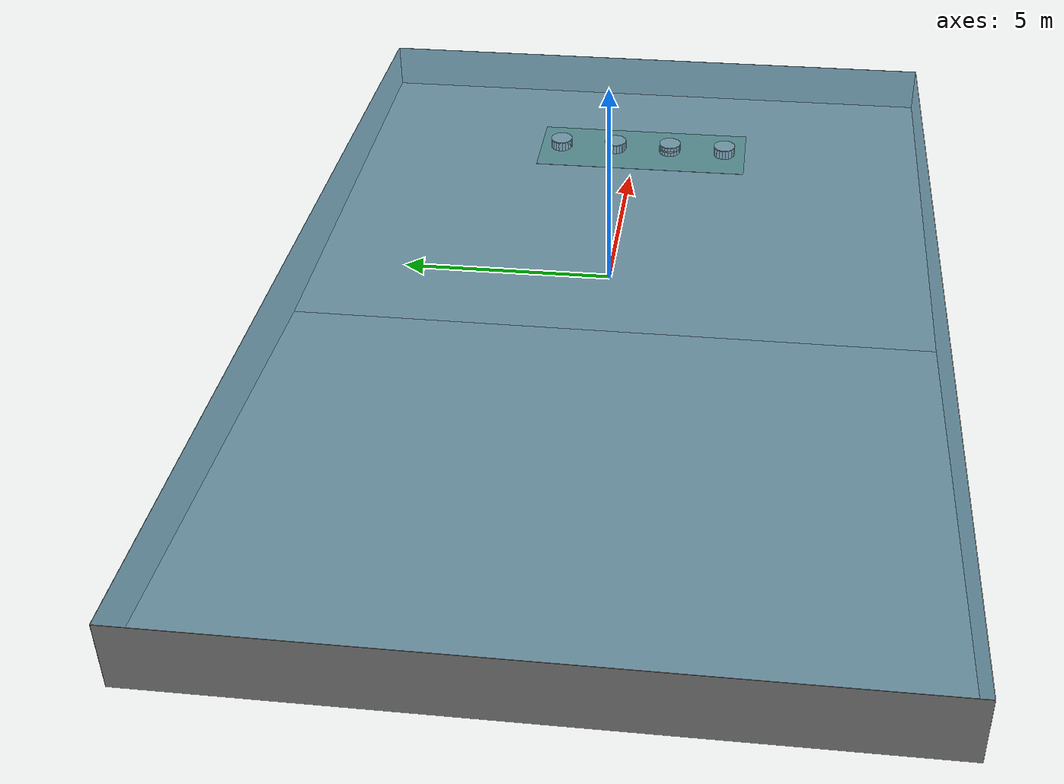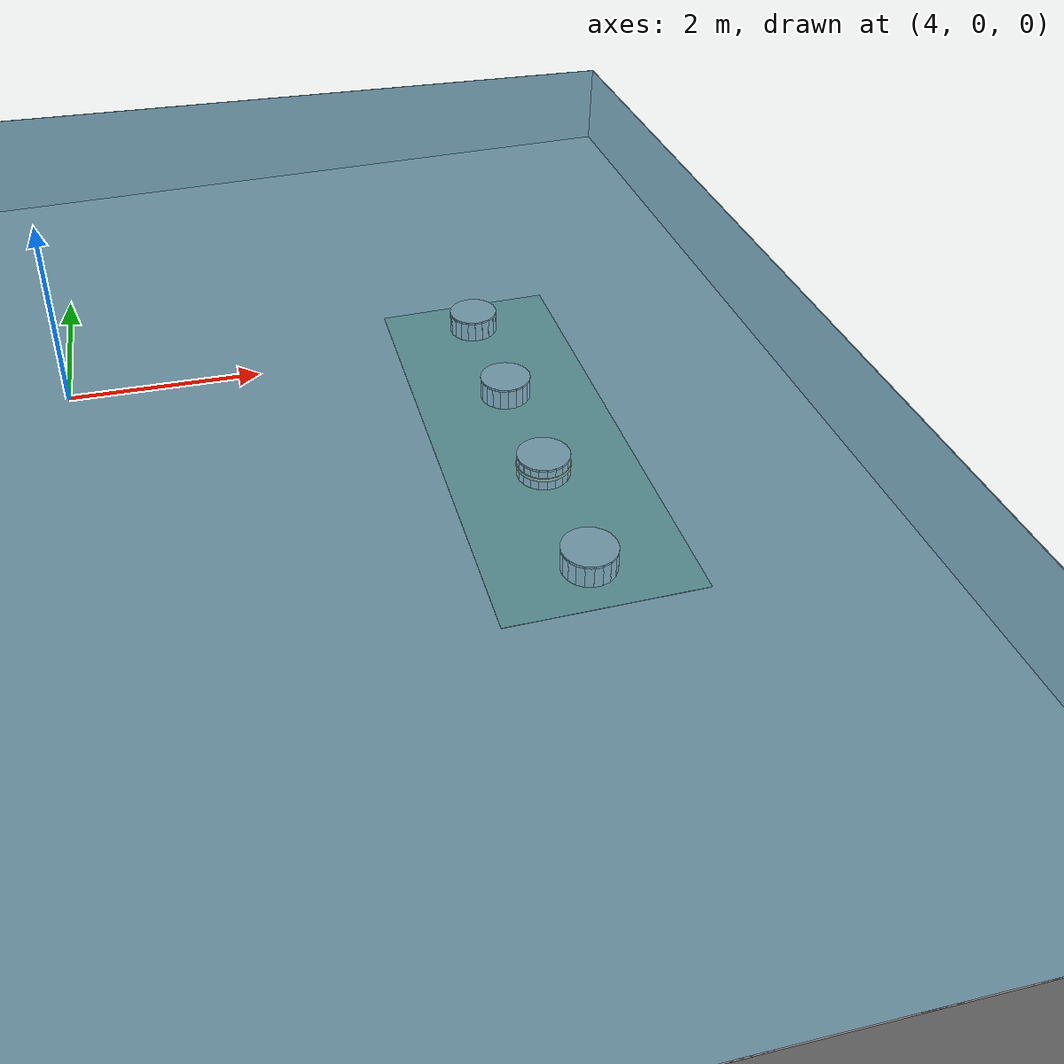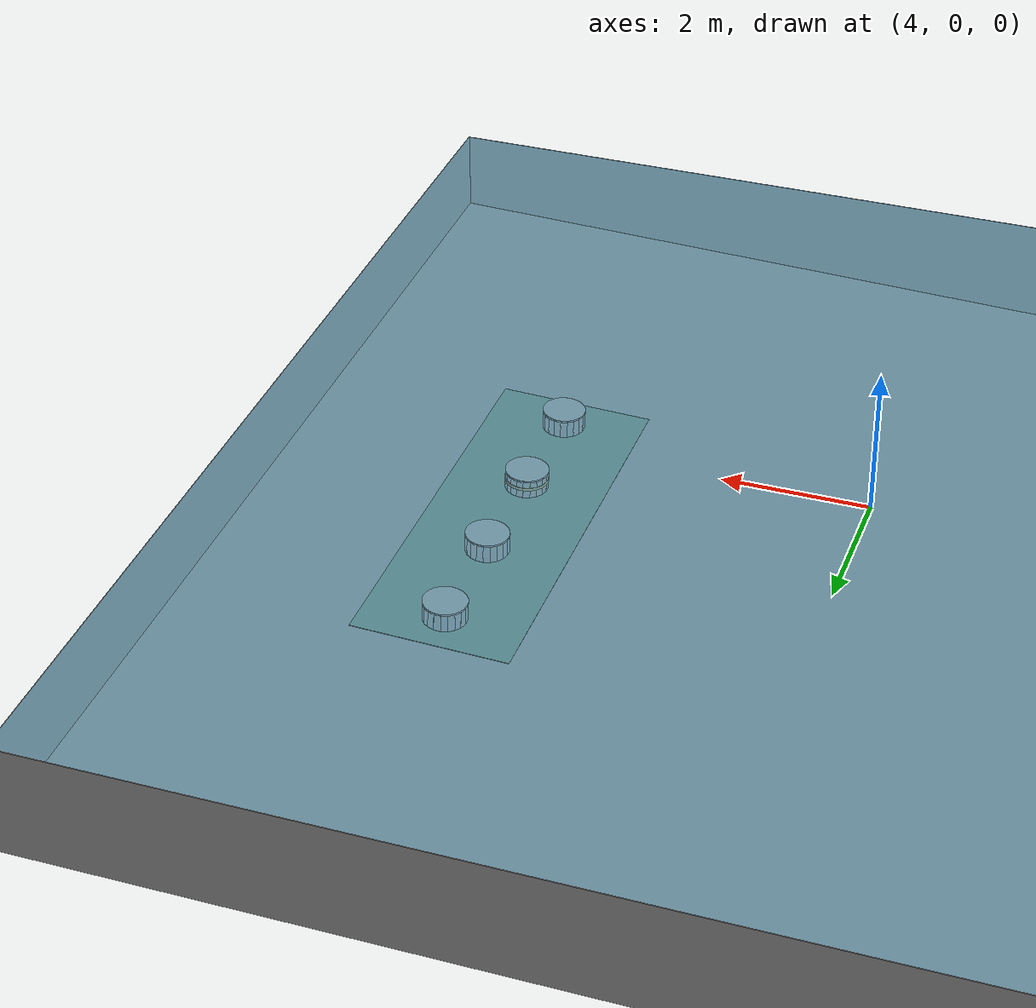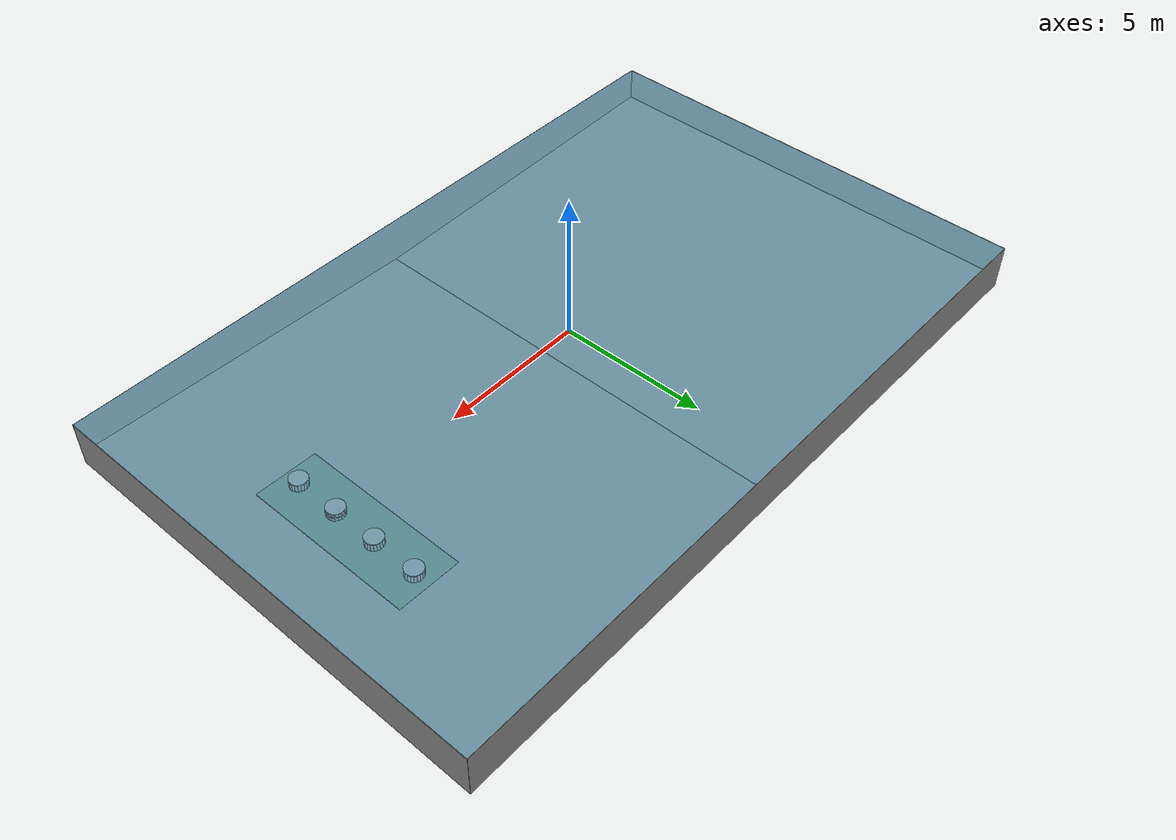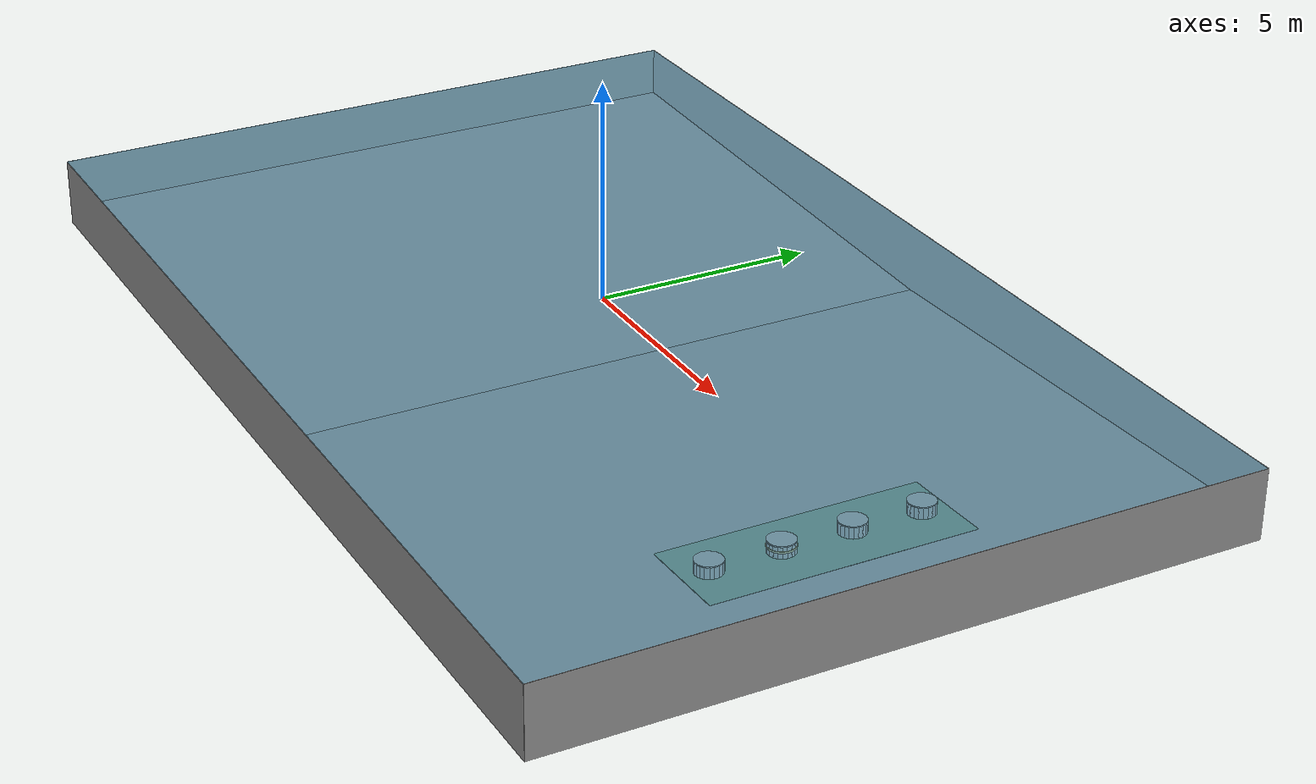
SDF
<sdf version="1.9">
 <world name="task_target_acquisition">
  <plugin filename="gz-sim-particle-emitter-system" name="gz::sim::systems::ParticleEmitter"/>
  <plugin filename="gz-sim-physics-system" name="gz::sim::systems::Physics"/>
  <plugin filename="gz-sim-user-commands-system" name="gz::sim::systems::UserCommands"/>
  <plugin filename="gz-sim-scene-broadcaster-system" name="gz::sim::systems::SceneBroadcaster"/>
  <plugin filename="gz-sim-apply-link-wrench-system" name="gz::sim::systems::ApplyLinkWrench"/>
  <plugin filename="gz-sim-imu-system" name="gz::sim::systems::Imu"/>
  <plugin filename="gz-sim-sensors-system" name="gz::sim::systems::Sensors">
   <render_engine>ogre2</render_engine>
  </plugin>
  <plugin filename="gz-sim-dvl-system" name="gz::sim::systems::DopplerVelocityLogSystem"/>
  <plugin filename="gz-sim-buoyancy-system" name="gz::sim::systems::Buoyancy">
   <graded_buoyancy>
    <default_density>1000</default_density>
    <density_change><above_depth>0</above_depth><density>1</density></density_change>
   </graded_buoyancy>
   <enable>duburi</enable>
   <enable>payload_shot_0</enable>
   <enable>payload_shot_1</enable>
   <enable>payload_shot_2</enable>
   <enable>payload_shot_3</enable>
   <enable>payload_shot_4</enable>
   <enable>payload_shot_5</enable>
   <enable>payload_shot_6</enable>
   <enable>payload_shot_7</enable>
   <enable>payload_shot_8</enable>
   <enable>payload_shot_9</enable>
   <enable>payload_shot_10</enable>
   <enable>payload_shot_11</enable>
  </plugin>
  <physics name="default" type="dart">
   <max_step_size>0.001</max_step_size>
   <real_time_factor>1.0</real_time_factor>
   <real_time_update_rate>1000</real_time_update_rate>
   <dart>
    <collision_detector>bullet</collision_detector>
    <solver><solver_type>dantzig</solver_type></solver>
   </dart>
  </physics>
  <gravity>0 0 -9.81</gravity>
  <magnetic_field>3.9e-05 1.1e-06 2.6e-05</magnetic_field>
  <atmosphere type="adiabatic"/>
  <scene>
   <ambient>0.28 0.4 0.48 1</ambient>
   <background>0.08 0.26 0.4 1</background>
   <shadows>true</shadows>
   <fog>
    <color>0.14 0.34 0.42 1</color>
    <type>linear</type>
    <start>2.0</start>
    <end>20.0</end>
    <density>0.02</density>
   </fog>
  </scene>
  <light type="directional" name="sun">
   <pose>0 0 10 0 0 0</pose>
   <diffuse>0.48 0.52 0.56 1</diffuse>
   <specular>0.10 0.10 0.11 1</specular>
   <direction>-0.4 0.15 -0.9</direction>
  </light>
  <light type="directional" name="fill">
   <cast_shadows>false</cast_shadows>
   <pose>0 0 5 0 0 0</pose>
   <diffuse>0.22 0.28 0.34 1</diffuse>
   <specular>0.04 0.05 0.06 1</specular>
   <direction>0.3 -0.2 -1</direction>
  </light>
  <light type="directional" name="caustic_fill">
   <cast_shadows>false</cast_shadows>
   <pose>0 0 3 0 0 0</pose>
   <diffuse>0.12 0.22 0.26 1</diffuse>
   <specular>0.02 0.03 0.04 1</specular>
   <direction>0.1 0.35 -0.85</direction>
  </light>
  <model name="sauvc_pool">
   <static>true</static>
   <link name="floor_neg">
    <pose>-6.25 0 -1.4 0 0.0319891 0</pose>
    <inertial>
     <mass>1000</mass>
     <inertia><ixx>1000</ixx><ixy>0</ixy><ixz>0</ixz><iyy>1000</iyy><iyz>0</iyz><izz>1000</izz></inertia>
    </inertial>
    <visual name="floor_neg_visual">
     <pose>0 0 0.005 0 0 0</pose>
     <geometry><box><size>12.5064 16 0.01</size></box></geometry>
     <material>
      <ambient>0.55 0.55 0.55 1</ambient>
      <diffuse>0.55 0.55 0.55 1</diffuse>
      <specular>0.08 0.08 0.08 1</specular>
      <emissive>0 0 0 1</emissive>
      <pbr>
       <metal>
        <albedo_map>model://sauvc_textures/pool_floor_neg.png</albedo_map>
        <metalness>0.0</metalness>
        <roughness>0.85</roughness>
       </metal>
      </pbr>
     </material>
    </visual>
    <collision name="floor_neg_collision">
     <pose>0 0 -0.05 0 0 0</pose>
     <geometry><box><size>12.5064 16 0.1</size></box></geometry>
    </collision>
   </link>
   <link name="floor_pos">
    <pose>6.25 0 -1.4 0 -0.0319891 0</pose>
    <inertial>
     <mass>1000</mass>
     <inertia><ixx>1000</ixx><ixy>0</ixy><ixz>0</ixz><iyy>1000</iyy><iyz>0</iyz><izz>1000</izz></inertia>
    </inertial>
    <visual name="floor_pos_visual">
     <pose>0 0 0.005 0 0 0</pose>
     <geometry><box><size>12.5064 16 0.01</size></box></geometry>
     <material>
      <ambient>0.55 0.55 0.55 1</ambient>
      <diffuse>0.55 0.55 0.55 1</diffuse>
      <specular>0.08 0.08 0.08 1</specular>
      <emissive>0 0 0 1</emissive>
      <pbr>
       <metal>
        <albedo_map>model://sauvc_textures/pool_floor_pos.png</albedo_map>
        <metalness>0.0</metalness>
        <roughness>0.85</roughness>
       </metal>
      </pbr>
     </material>
    </visual>
    <collision name="floor_pos_collision">
     <pose>0 0 -0.05 0 0 0</pose>
     <geometry><box><size>12.5064 16 0.1</size></box></geometry>
    </collision>
   </link>
   <link name="wall_x_pos">
    <inertial>
     <mass>1000</mass>
     <inertia><ixx>1000</ixx><ixy>0</ixy><ixz>0</ixz><iyy>1000</iyy><iyz>0</iyz><izz>1000</izz></inertia>
    </inertial>
    <visual name="wall_x_pos_visual">
     <pose>12.5 0 -0.8 0 0 0</pose>
     <geometry><box><size>0.01 16 1.6</size></box></geometry>
     <material>
      <ambient>0.55 0.55 0.55 1</ambient>
      <diffuse>0.55 0.55 0.55 1</diffuse>
      <specular>0.08 0.08 0.08 1</specular>
      <emissive>0 0 0 1</emissive>
      <pbr>
       <metal>
        <albedo_map>model://sauvc_textures/pool_wall_long.png</albedo_map>
        <metalness>0.0</metalness>
        <roughness>0.85</roughness>
       </metal>
      </pbr>
     </material>
    </visual>
    <collision name="wall_x_pos_collision">
     <pose>12.605 0 -0.8 0 0 0</pose>
     <geometry><box><size>0.2 16.4 1.6</size></box></geometry>
    </collision>
   </link>
   <link name="wall_x_neg">
    <inertial>
     <mass>1000</mass>
     <inertia><ixx>1000</ixx><ixy>0</ixy><ixz>0</ixz><iyy>1000</iyy><iyz>0</iyz><izz>1000</izz></inertia>
    </inertial>
    <visual name="wall_x_neg_visual">
     <pose>-12.5 0 -0.8 0 0 0</pose>
     <geometry><box><size>0.01 16 1.6</size></box></geometry>
     <material>
      <ambient>0.55 0.55 0.55 1</ambient>
      <diffuse>0.55 0.55 0.55 1</diffuse>
      <specular>0.08 0.08 0.08 1</specular>
      <emissive>0 0 0 1</emissive>
      <pbr>
       <metal>
        <albedo_map>model://sauvc_textures/pool_wall_long.png</albedo_map>
        <metalness>0.0</metalness>
        <roughness>0.85</roughness>
       </metal>
      </pbr>
     </material>
    </visual>
    <collision name="wall_x_neg_collision">
     <pose>-12.605 0 -0.8 0 0 0</pose>
     <geometry><box><size>0.2 16.4 1.6</size></box></geometry>
    </collision>
   </link>
   <link name="wall_y_pos">
    <inertial>
     <mass>1000</mass>
     <inertia><ixx>1000</ixx><ixy>0</ixy><ixz>0</ixz><iyy>1000</iyy><iyz>0</iyz><izz>1000</izz></inertia>
    </inertial>
    <visual name="wall_y_pos_visual">
     <pose>0 8 -0.8 0 0 0</pose>
     <geometry><box><size>25 0.01 1.6</size></box></geometry>
     <material>
      <ambient>0.55 0.55 0.55 1</ambient>
      <diffuse>0.55 0.55 0.55 1</diffuse>
      <specular>0.08 0.08 0.08 1</specular>
      <emissive>0 0 0 1</emissive>
      <pbr>
       <metal>
        <albedo_map>model://sauvc_textures/pool_wall_short.png</albedo_map>
        <metalness>0.0</metalness>
        <roughness>0.85</roughness>
       </metal>
      </pbr>
     </material>
    </visual>
    <collision name="wall_y_pos_collision">
     <pose>0 8.105 -0.8 0 0 0</pose>
     <geometry><box><size>25 0.2 1.6</size></box></geometry>
    </collision>
   </link>
   <link name="wall_y_neg">
    <inertial>
     <mass>1000</mass>
     <inertia><ixx>1000</ixx><ixy>0</ixy><ixz>0</ixz><iyy>1000</iyy><iyz>0</iyz><izz>1000</izz></inertia>
    </inertial>
    <visual name="wall_y_neg_visual">
     <pose>0 -8 -0.8 0 0 0</pose>
     <geometry><box><size>25 0.01 1.6</size></box></geometry>
     <material>
      <ambient>0.55 0.55 0.55 1</ambient>
      <diffuse>0.55 0.55 0.55 1</diffuse>
      <specular>0.08 0.08 0.08 1</specular>
      <emissive>0 0 0 1</emissive>
      <pbr>
       <metal>
        <albedo_map>model://sauvc_textures/pool_wall_short.png</albedo_map>
        <metalness>0.0</metalness>
        <roughness>0.85</roughness>
       </metal>
      </pbr>
     </material>
    </visual>
    <collision name="wall_y_neg_collision">
     <pose>0 -8.105 -0.8 0 0 0</pose>
     <geometry><box><size>25 0.2 1.6</size></box></geometry>
    </collision>
   </link>
   <link name="water_surface">
    <inertial>
     <mass>1</mass>
     <inertia><ixx>1</ixx><ixy>0</ixy><ixz>0</ixz><iyy>1</iyy><iyz>0</iyz><izz>1</izz></inertia>
    </inertial>
    <visual name="water_surface_visual">
     <cast_shadows>false</cast_shadows>
     <transparency>0.18</transparency>
     <geometry><mesh><uri>model://robosub_meshes/meshes/water_sauvc.obj</uri></mesh></geometry>
     <material>
      <ambient>0.42 0.6 0.68 1</ambient>
      <diffuse>0.42 0.6 0.68 1</diffuse>
      <specular>0.35 0.35 0.35 1</specular>
      <emissive>0.1 0.1 0.1 1</emissive>
      <pbr>
       <metal>
        <albedo_map>model://sauvc_textures/water_surface.png</albedo_map>
        <metalness>0.0</metalness>
        <roughness>0.15</roughness>
       </metal>
      </pbr>
     </material>
    </visual>
   </link>
  </model>
  <model name="marine_snow">
   <static>true</static>
   <pose>0 0 -0.8 0 0 0</pose>
   <link name="link">
    <particle_emitter name="snow" type="box">
     <emitting>true</emitting>
     <size>12 12 1.6</size>
     <particle_size>0.006 0.006 0.006</particle_size>
     <lifetime>30</lifetime>
     <min_velocity>0.004</min_velocity>
     <max_velocity>0.025</max_velocity>
     <scale_rate>0</scale_rate>
     <rate>900</rate>
     <topic>marine_snow</topic>
     <material>
      <diffuse>0.80 0.84 0.80</diffuse>
      <specular>0.05 0.05 0.05</specular>
      <pbr><metal><albedo_map>model://sauvc_textures/marine_snow.png</albedo_map></metal></pbr>
     </material>
    </particle_emitter>
   </link>
  </model>
  <include>
   <uri>model://sauvc_target_mat</uri>
   <name>target_mat</name>
   <pose>9 0 -1.312 -0.0319891 1.17502e-07 1.5708</pose>
  </include>
  <include>
   <uri>model://sauvc_drum_red</uri>
   <name>drum_a</name>
   <pose>9 2.4 -1.312 -0 -0.0319891 0</pose>
  </include>
  <include>
   <uri>model://sauvc_drum_blue</uri>
   <name>drum_b</name>
   <pose>9 0.8 -1.312 -0 -0.0319891 0</pose>
  </include>
  <include>
   <uri>model://sauvc_drum_red_pinger</uri>
   <name>drum_c</name>
   <pose>9 -0.8 -1.312 -0 -0.0319891 0</pose>
  </include>
  <include>
   <uri>model://sauvc_drum_red</uri>
   <name>drum_d</name>
   <pose>9 -2.4 -1.312 -0 -0.0319891 0</pose>
  </include>
 </world>
</sdf>

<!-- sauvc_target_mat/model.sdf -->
<sdf version="1.9">
  <model name="sauvc_target_mat">
    <static>true</static>
    <plugin filename="gz-sim-label-system" name="gz::sim::systems::Label">
      <label>11</label>
    </plugin>
    <link name="mat">
      <pose>0 0 0.02 0 0 0</pose>
      <inertial>
        <pose>0 0 0 0 0 0</pose>
        <mass>0.001</mass>
        <inertia>
          <ixx>1e-06</ixx><ixy>0</ixy><ixz>0</ixz>
          <iyy>1e-06</iyy><iyz>0</iyz>
          <izz>1e-06</izz>
        </inertia>
      </inertial>
      <visual name="mat_visual">
        <pose>0 0 0 0 0 0</pose>
        <geometry><box><size>6 2.2 0.006</size></box></geometry>
        <material>
          <ambient>0.13 0.45 0.2 1</ambient>
          <diffuse>0.13 0.45 0.2 1</diffuse>
          <specular>0.06 0.06 0.06 1</specular>
          <emissive>0.14 0.14 0.14 1</emissive>
          <pbr>
            <metal>
              <albedo_map>model://sauvc_textures/albedo_fabric.png</albedo_map>
              <metalness>0.0</metalness>
              <roughness_map>model://sauvc_textures/rough_fabric.png</roughness_map>
              <normal_map>model://sauvc_textures/norm_fabric.png</normal_map>
            </metal>
          </pbr>
        </material>
      </visual>
    </link>
  </model>
</sdf>

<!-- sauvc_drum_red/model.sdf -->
<sdf version="1.9">
  <model name="sauvc_drum_red">
    <static>true</static>
    <plugin filename="gz-sim-label-system" name="gz::sim::systems::Label">
      <label>7</label>
    </plugin>
    <link name="base">
      <pose>0 0 0.01 0 0 0</pose>
      <inertial>
        <pose>0 0 0 0 0 0</pose>
        <mass>3</mass>
        <inertia>
          <ixx>0.0676</ixx><ixy>0</ixy><ixz>0</ixz>
          <iyy>0.0676</iyy><iyz>0</iyz>
          <izz>0.135</izz>
        </inertia>
      </inertial>
      <visual name="base_visual">
        <pose>0 0 0 0 0 0</pose>
        <geometry><cylinder><radius>0.3</radius><length>0.02</length></cylinder></geometry>
        <material>
          <ambient>0.8 0.1 0.1 1</ambient>
          <diffuse>0.8 0.1 0.1 1</diffuse>
          <specular>0.2 0.2 0.2 1</specular>
          <emissive>0.44 0.055 0.055 1</emissive>
        </material>
      </visual>
      <collision name="base_collision">
        <pose>0 0 0 0 0 0</pose>
        <geometry><cylinder><radius>0.3</radius><length>0.02</length></cylinder></geometry>
      </collision>
    </link>
    <link name="rim">
      <pose>0 0 0.288 0 0 0</pose>
      <inertial>
        <pose>0 0 0 0 0 0</pose>
        <mass>0.3</mass>
        <inertia>
          <ixx>0.0069925</ixx><ixy>0</ixy><ixz>0</ixz>
          <iyy>0.0069925</iyy><iyz>0</iyz>
          <izz>0.0139537</izz>
        </inertia>
      </inertial>
      <visual name="rim_visual">
        <pose>0 0 0 0 0 0</pose>
        <geometry><cylinder><radius>0.305</radius><length>0.025</length></cylinder></geometry>
        <material>
          <ambient>0.7 0.7 0.7 1</ambient>
          <diffuse>0.7 0.7 0.7 1</diffuse>
          <specular>0.35 0.35 0.35 1</specular>
          <emissive>0.08 0.08 0.08 1</emissive>
          <pbr>
            <metal>
              <albedo_map>model://sauvc_textures/drum_rim.png</albedo_map>
              <metalness>0.0</metalness>
              <roughness>0.4</roughness>
            </metal>
          </pbr>
        </material>
      </visual>
    </link>
    <link name="wall_0">
      <pose>0.29 0 0.15 0 0 0.000000</pose>
      <inertial>
        <pose>0 0 0 0 0 0</pose>
        <mass>0.2</mass>
        <inertia>
          <ixx>0.00166188</ixx><ixy>0</ixy><ixz>0</ixz>
          <iyy>0.00150667</iyy><iyz>0</iyz>
          <izz>0.000168547</izz>
        </inertia>
      </inertial>
      <visual name="wall_0_visual">
        <pose>0 0 0 0 0 0</pose>
        <geometry><box><size>0.02 0.0985537 0.3</size></box></geometry>
        <material>
          <ambient>0.72 0.72 0.72 1</ambient>
          <diffuse>0.72 0.72 0.72 1</diffuse>
          <specular>0.14 0.14 0.14 1</specular>
          <emissive>0.1 0.1 0.1 1</emissive>
          <pbr>
            <metal>
              <albedo_map>model://sauvc_textures/drum_wall_red.png</albedo_map>
              <metalness>0.0</metalness>
              <roughness_map>model://sauvc_textures/rough_plastic.png</roughness_map>
            </metal>
          </pbr>
        </material>
      </visual>
    </link>
    <link name="wall_1">
      <pose>0.275806 0.0896149 0.15 0 0 0.314159</pose>
      <inertial>
        <pose>0 0 0 0 0 0</pose>
        <mass>0.2</mass>
        <inertia>
          <ixx>0.00166188</ixx><ixy>0</ixy><ixz>0</ixz>
          <iyy>0.00150667</iyy><iyz>0</iyz>
          <izz>0.000168547</izz>
        </inertia>
      </inertial>
      <visual name="wall_1_visual">
        <pose>0 0 0 0 0 0</pose>
        <geometry><box><size>0.02 0.0985537 0.3</size></box></geometry>
        <material>
          <ambient>0.72 0.72 0.72 1</ambient>
          <diffuse>0.72 0.72 0.72 1</diffuse>
          <specular>0.14 0.14 0.14 1</specular>
          <emissive>0.1 0.1 0.1 1</emissive>
          <pbr>
            <metal>
              <albedo_map>model://sauvc_textures/drum_wall_red.png</albedo_map>
              <metalness>0.0</metalness>
              <roughness_map>model://sauvc_textures/rough_plastic.png</roughness_map>
            </metal>
          </pbr>
        </material>
      </visual>
    </link>
    <link name="wall_2">
      <pose>0.234615 0.170458 0.15 0 0 0.628319</pose>
      <inertial>
        <pose>0 0 0 0 0 0</pose>
        <mass>0.2</mass>
        <inertia>
          <ixx>0.00166188</ixx><ixy>0</ixy><ixz>0</ixz>
          <iyy>0.00150667</iyy><iyz>0</iyz>
          <izz>0.000168547</izz>
        </inertia>
      </inertial>
      <visual name="wall_2_visual">
        <pose>0 0 0 0 0 0</pose>
        <geometry><box><size>0.02 0.0985537 0.3</size></box></geometry>
        <material>
          <ambient>0.72 0.72 0.72 1</ambient>
          <diffuse>0.72 0.72 0.72 1</diffuse>
          <specular>0.14 0.14 0.14 1</specular>
          <emissive>0.1 0.1 0.1 1</emissive>
          <pbr>
            <metal>
              <albedo_map>model://sauvc_textures/drum_wall_red.png</albedo_map>
              <metalness>0.0</metalness>
              <roughness_map>model://sauvc_textures/rough_plastic.png</roughness_map>
            </metal>
          </pbr>
        </material>
      </visual>
    </link>
    <link name="wall_3">
      <pose>0.170458 0.234615 0.15 0 0 0.942478</pose>
      <inertial>
        <pose>0 0 0 0 0 0</pose>
        <mass>0.2</mass>
        <inertia>
          <ixx>0.00166188</ixx><ixy>0</ixy><ixz>0</ixz>
          <iyy>0.00150667</iyy><iyz>0</iyz>
          <izz>0.000168547</izz>
        </inertia>
      </inertial>
      <visual name="wall_3_visual">
        <pose>0 0 0 0 0 0</pose>
        <geometry><box><size>0.02 0.0985537 0.3</size></box></geometry>
        <material>
          <ambient>0.72 0.72 0.72 1</ambient>
          <diffuse>0.72 0.72 0.72 1</diffuse>
          <specular>0.14 0.14 0.14 1</specular>
          <emissive>0.1 0.1 0.1 1</emissive>
          <pbr>
            <metal>
              <albedo_map>model://sauvc_textures/drum_wall_red.png</albedo_map>
              <metalness>0.0</metalness>
              <roughness_map>model://sauvc_textures/rough_plastic.png</roughness_map>
            </metal>
          </pbr>
        </material>
      </visual>
    </link>
    <link name="wall_4">
      <pose>0.0896149 0.275806 0.15 0 0 1.256637</pose>
      <inertial>
        <pose>0 0 0 0 0 0</pose>
        <mass>0.2</mass>
        <inertia>
          <ixx>0.00166188</ixx><ixy>0</ixy><ixz>0</ixz>
          <iyy>0.00150667</iyy><iyz>0</iyz>
          <izz>0.000168547</izz>
        </inertia>
      </inertial>
      <visual name="wall_4_visual">
        <pose>0 0 0 0 0 0</pose>
        <geometry><box><size>0.02 0.0985537 0.3</size></box></geometry>
        <material>
          <ambient>0.72 0.72 0.72 1</ambient>
          <diffuse>0.72 0.72 0.72 1</diffuse>
          <specular>0.14 0.14 0.14 1</specular>
          <emissive>0.1 0.1 0.1 1</emissive>
          <pbr>
            <metal>
              <albedo_map>model://sauvc_textures/drum_wall_red.png</albedo_map>
              <metalness>0.0</metalness>
              <roughness_map>model://sauvc_textures/rough_plastic.png</roughness_map>
            </metal>
          </pbr>
        </material>
      </visual>
    </link>
    <link name="wall_5">
      <pose>1.77574e-17 0.29 0.15 0 0 1.570796</pose>
      <inertial>
        <pose>0 0 0 0 0 0</pose>
        <mass>0.2</mass>
        <inertia>
          <ixx>0.00166188</ixx><ixy>0</ixy><ixz>0</ixz>
          <iyy>0.00150667</iyy><iyz>0</iyz>
          <izz>0.000168547</izz>
        </inertia>
      </inertial>
      <visual name="wall_5_visual">
        <pose>0 0 0 0 0 0</pose>
        <geometry><box><size>0.02 0.0985537 0.3</size></box></geometry>
        <material>
          <ambient>0.72 0.72 0.72 1</ambient>
          <diffuse>0.72 0.72 0.72 1</diffuse>
          <specular>0.14 0.14 0.14 1</specular>
          <emissive>0.1 0.1 0.1 1</emissive>
          <pbr>
            <metal>
              <albedo_map>model://sauvc_textures/drum_wall_red.png</albedo_map>
              <metalness>0.0</metalness>
              <roughness_map>model://sauvc_textures/rough_plastic.png</roughness_map>
            </metal>
          </pbr>
        </material>
      </visual>
    </link>
    <link name="wall_6">
      <pose>-0.0896149 0.275806 0.15 0 0 1.884956</pose>
      <inertial>
        <pose>0 0 0 0 0 0</pose>
        <mass>0.2</mass>
        <inertia>
          <ixx>0.00166188</ixx><ixy>0</ixy><ixz>0</ixz>
          <iyy>0.00150667</iyy><iyz>0</iyz>
          <izz>0.000168547</izz>
        </inertia>
      </inertial>
      <visual name="wall_6_visual">
        <pose>0 0 0 0 0 0</pose>
        <geometry><box><size>0.02 0.0985537 0.3</size></box></geometry>
        <material>
          <ambient>0.72 0.72 0.72 1</ambient>
          <diffuse>0.72 0.72 0.72 1</diffuse>
          <specular>0.14 0.14 0.14 1</specular>
          <emissive>0.1 0.1 0.1 1</emissive>
          <pbr>
            <metal>
              <albedo_map>model://sauvc_textures/drum_wall_red.png</albedo_map>
              <metalness>0.0</metalness>
              <roughness_map>model://sauvc_textures/rough_plastic.png</roughness_map>
            </metal>
          </pbr>
        </material>
      </visual>
    </link>
    <link name="wall_7">
      <pose>-0.170458 0.234615 0.15 0 0 2.199115</pose>
      <inertial>
        <pose>0 0 0 0 0 0</pose>
        <mass>0.2</mass>
        <inertia>
          <ixx>0.00166188</ixx><ixy>0</ixy><ixz>0</ixz>
          <iyy>0.00150667</iyy><iyz>0</iyz>
          <izz>0.000168547</izz>
        </inertia>
      </inertial>
      <visual name="wall_7_visual">
        <pose>0 0 0 0 0 0</pose>
        <geometry><box><size>0.02 0.0985537 0.3</size></box></geometry>
        <material>
          <ambient>0.72 0.72 0.72 1</ambient>
          <diffuse>0.72 0.72 0.72 1</diffuse>
          <specular>0.14 0.14 0.14 1</specular>
          <emissive>0.1 0.1 0.1 1</emissive>
          <pbr>
            <metal>
              <albedo_map>model://sauvc_textures/drum_wall_red.png</albedo_map>
              <metalness>0.0</metalness>
              <roughness_map>model://sauvc_textures/rough_plastic.png</roughness_map>
            </metal>
          </pbr>
        </material>
      </visual>
    </link>
    <link name="wall_8">
      <pose>-0.234615 0.170458 0.15 0 0 2.513274</pose>
      <inertial>
        <pose>0 0 0 0 0 0</pose>
        <mass>0.2</mass>
        <inertia>
          <ixx>0.00166188</ixx><ixy>0</ixy><ixz>0</ixz>
          <iyy>0.00150667</iyy><iyz>0</iyz>
          <izz>0.000168547</izz>
        </inertia>
      </inertial>
      <visual name="wall_8_visual">
        <pose>0 0 0 0 0 0</pose>
        <geometry><box><size>0.02 0.0985537 0.3</size></box></geometry>
        <material>
          <ambient>0.72 0.72 0.72 1</ambient>
          <diffuse>0.72 0.72 0.72 1</diffuse>
          <specular>0.14 0.14 0.14 1</specular>
          <emissive>0.1 0.1 0.1 1</emissive>
          <pbr>
            <metal>
              <albedo_map>model://sauvc_textures/drum_wall_red.png</albedo_map>
              <metalness>0.0</metalness>
              <roughness_map>model://sauvc_textures/rough_plastic.png</roughness_map>
            </metal>
          </pbr>
        </material>
      </visual>
    </link>
    <link name="wall_9">
      <pose>-0.275806 0.0896149 0.15 0 0 2.827433</pose>
      <inertial>
        <pose>0 0 0 0 0 0</pose>
        <mass>0.2</mass>
        <inertia>
          <ixx>0.00166188</ixx><ixy>0</ixy><ixz>0</ixz>
          <iyy>0.00150667</iyy><iyz>0</iyz>
          <izz>0.000168547</izz>
        </inertia>
      </inertial>
      <visual name="wall_9_visual">
        <pose>0 0 0 0 0 0</pose>
        <geometry><box><size>0.02 0.0985537 0.3</size></box></geometry>
        <material>
          <ambient>0.72 0.72 0.72 1</ambient>
          <diffuse>0.72 0.72 0.72 1</diffuse>
          <specular>0.14 0.14 0.14 1</specular>
          <emissive>0.1 0.1 0.1 1</emissive>
          <pbr>
            <metal>
              <albedo_map>model://sauvc_textures/drum_wall_red.png</albedo_map>
              <metalness>0.0</metalness>
              <roughness_map>model://sauvc_textures/rough_plastic.png</roughness_map>
            </metal>
          </pbr>
        </material>
      </visual>
    </link>
    <link name="wall_10">
      <pose>-0.29 3.55148e-17 0.15 0 0 3.141593</pose>
      <inertial>
        <pose>0 0 0 0 0 0</pose>
        <mass>0.2</mass>
        <inertia>
          <ixx>0.00166188</ixx><ixy>0</ixy><ixz>0</ixz>
          <iyy>0.00150667</iyy><iyz>0</iyz>
          <izz>0.000168547</izz>
        </inertia>
      </inertial>
      <visual name="wall_10_visual">
        <pose>0 0 0 0 0 0</pose>
        <geometry><box><size>0.02 0.0985537 0.3</size></box></geometry>
        <material>
          <ambient>0.72 0.72 0.72 1</ambient>
          <diffuse>0.72 0.72 0.72 1</diffuse>
          <specular>0.14 0.14 0.14 1</specular>
          <emissive>0.1 0.1 0.1 1</emissive>
          <pbr>
            <metal>
              <albedo_map>model://sauvc_textures/drum_wall_red.png</albedo_map>
              <metalness>0.0</metalness>
              <roughness_map>model://sauvc_textures/rough_plastic.png</roughness_map>
            </metal>
          </pbr>
        </material>
      </visual>
    </link>
    <link name="wall_11">
      <pose>-0.275806 -0.0896149 0.15 0 0 3.455752</pose>
      <inertial>
        <pose>0 0 0 0 0 0</pose>
        <mass>0.2</mass>
        <inertia>
          <ixx>0.00166188</ixx><ixy>0</ixy><ixz>0</ixz>
          <iyy>0.00150667</iyy><iyz>0</iyz>
          <izz>0.000168547</izz>
        </inertia>
      </inertial>
      <visual name="wall_11_visual">
        <pose>0 0 0 0 0 0</pose>
        <geometry><box><size>0.02 0.0985537 0.3</size></box></geometry>
        <material>
          <ambient>0.72 0.72 0.72 1</ambient>
          <diffuse>0.72 0.72 0.72 1</diffuse>
          <specular>0.14 0.14 0.14 1</specular>
          <emissive>0.1 0.1 0.1 1</emissive>
          <pbr>
            <metal>
              <albedo_map>model://sauvc_textures/drum_wall_red.png</albedo_map>
              <metalness>0.0</metalness>
              <roughness_map>model://sauvc_textures/rough_plastic.png</roughness_map>
            </metal>
          </pbr>
        </material>
      </visual>
    </link>
    <link name="wall_12">
      <pose>-0.234615 -0.170458 0.15 0 0 3.769911</pose>
      <inertial>
        <pose>0 0 0 0 0 0</pose>
        <mass>0.2</mass>
        <inertia>
          <ixx>0.00166188</ixx><ixy>0</ixy><ixz>0</ixz>
          <iyy>0.00150667</iyy><iyz>0</iyz>
          <izz>0.000168547</izz>
        </inertia>
      </inertial>
      <visual name="wall_12_visual">
        <pose>0 0 0 0 0 0</pose>
        <geometry><box><size>0.02 0.0985537 0.3</size></box></geometry>
        <material>
          <ambient>0.72 0.72 0.72 1</ambient>
          <diffuse>0.72 0.72 0.72 1</diffuse>
          <specular>0.14 0.14 0.14 1</specular>
          <emissive>0.1 0.1 0.1 1</emissive>
          <pbr>
            <metal>
              <albedo_map>model://sauvc_textures/drum_wall_red.png</albedo_map>
              <metalness>0.0</metalness>
              <roughness_map>model://sauvc_textures/rough_plastic.png</roughness_map>
            </metal>
          </pbr>
        </material>
      </visual>
    </link>
    <link name="wall_13">
      <pose>-0.170458 -0.234615 0.15 0 0 4.084070</pose>
      <inertial>
        <pose>0 0 0 0 0 0</pose>
        <mass>0.2</mass>
        <inertia>
          <ixx>0.00166188</ixx><ixy>0</ixy><ixz>0</ixz>
          <iyy>0.00150667</iyy><iyz>0</iyz>
          <izz>0.000168547</izz>
        </inertia>
      </inertial>
      <visual name="wall_13_visual">
        <pose>0 0 0 0 0 0</pose>
        <geometry><box><size>0.02 0.0985537 0.3</size></box></geometry>
        <material>
          <ambient>0.72 0.72 0.72 1</ambient>
          <diffuse>0.72 0.72 0.72 1</diffuse>
          <specular>0.14 0.14 0.14 1</specular>
          <emissive>0.1 0.1 0.1 1</emissive>
          <pbr>
            <metal>
              <albedo_map>model://sauvc_textures/drum_wall_red.png</albedo_map>
              <metalness>0.0</metalness>
              <roughness_map>model://sauvc_textures/rough_plastic.png</roughness_map>
            </metal>
          </pbr>
        </material>
      </visual>
    </link>
    <link name="wall_14">
      <pose>-0.0896149 -0.275806 0.15 0 0 4.398230</pose>
      <inertial>
        <pose>0 0 0 0 0 0</pose>
        <mass>0.2</mass>
        <inertia>
          <ixx>0.00166188</ixx><ixy>0</ixy><ixz>0</ixz>
          <iyy>0.00150667</iyy><iyz>0</iyz>
          <izz>0.000168547</izz>
        </inertia>
      </inertial>
      <visual name="wall_14_visual">
        <pose>0 0 0 0 0 0</pose>
        <geometry><box><size>0.02 0.0985537 0.3</size></box></geometry>
        <material>
          <ambient>0.72 0.72 0.72 1</ambient>
          <diffuse>0.72 0.72 0.72 1</diffuse>
          <specular>0.14 0.14 0.14 1</specular>
          <emissive>0.1 0.1 0.1 1</emissive>
          <pbr>
            <metal>
              <albedo_map>model://sauvc_textures/drum_wall_red.png</albedo_map>
              <metalness>0.0</metalness>
              <roughness_map>model://sauvc_textures/rough_plastic.png</roughness_map>
            </metal>
          </pbr>
        </material>
      </visual>
    </link>
    <link name="wall_15">
      <pose>-5.32721e-17 -0.29 0.15 0 0 4.712389</pose>
      <inertial>
        <pose>0 0 0 0 0 0</pose>
        <mass>0.2</mass>
        <inertia>
          <ixx>0.00166188</ixx><ixy>0</ixy><ixz>0</ixz>
          <iyy>0.00150667</iyy><iyz>0</iyz>
          <izz>0.000168547</izz>
        </inertia>
      </inertial>
      <visual name="wall_15_visual">
        <pose>0 0 0 0 0 0</pose>
        <geometry><box><size>0.02 0.0985537 0.3</size></box></geometry>
        <material>
          <ambient>0.72 0.72 0.72 1</ambient>
          <diffuse>0.72 0.72 0.72 1</diffuse>
          <specular>0.14 0.14 0.14 1</specular>
          <emissive>0.1 0.1 0.1 1</emissive>
          <pbr>
            <metal>
              <albedo_map>model://sauvc_textures/drum_wall_red.png</albedo_map>
              <metalness>0.0</metalness>
              <roughness_map>model://sauvc_textures/rough_plastic.png</roughness_map>
            </metal>
          </pbr>
        </material>
      </visual>
    </link>
    <link name="wall_16">
      <pose>0.0896149 -0.275806 0.15 0 0 5.026548</pose>
      <inertial>
        <pose>0 0 0 0 0 0</pose>
        <mass>0.2</mass>
        <inertia>
          <ixx>0.00166188</ixx><ixy>0</ixy><ixz>0</ixz>
          <iyy>0.00150667</iyy><iyz>0</iyz>
          <izz>0.000168547</izz>
        </inertia>
      </inertial>
      <visual name="wall_16_visual">
        <pose>0 0 0 0 0 0</pose>
        <geometry><box><size>0.02 0.0985537 0.3</size></box></geometry>
        <material>
          <ambient>0.72 0.72 0.72 1</ambient>
          <diffuse>0.72 0.72 0.72 1</diffuse>
          <specular>0.14 0.14 0.14 1</specular>
          <emissive>0.1 0.1 0.1 1</emissive>
          <pbr>
            <metal>
              <albedo_map>model://sauvc_textures/drum_wall_red.png</albedo_map>
              <metalness>0.0</metalness>
              <roughness_map>model://sauvc_textures/rough_plastic.png</roughness_map>
            </metal>
          </pbr>
        </material>
      </visual>
    </link>
    <link name="wall_17">
      <pose>0.170458 -0.234615 0.15 0 0 5.340708</pose>
      <inertial>
        <pose>0 0 0 0 0 0</pose>
        <mass>0.2</mass>
        <inertia>
          <ixx>0.00166188</ixx><ixy>0</ixy><ixz>0</ixz>
          <iyy>0.00150667</iyy><iyz>0</iyz>
          <izz>0.000168547</izz>
        </inertia>
      </inertial>
      <visual name="wall_17_visual">
        <pose>0 0 0 0 0 0</pose>
        <geometry><box><size>0.02 0.0985537 0.3</size></box></geometry>
        <material>
          <ambient>0.72 0.72 0.72 1</ambient>
          <diffuse>0.72 0.72 0.72 1</diffuse>
          <specular>0.14 0.14 0.14 1</specular>
          <emissive>0.1 0.1 0.1 1</emissive>
          <pbr>
            <metal>
              <albedo_map>model://sauvc_textures/drum_wall_red.png</albedo_map>
              <metalness>0.0</metalness>
              <roughness_map>model://sauvc_textures/rough_plastic.png</roughness_map>
            </metal>
          </pbr>
        </material>
      </visual>
    </link>
    <link name="wall_18">
      <pose>0.234615 -0.170458 0.15 0 0 5.654867</pose>
      <inertial>
        <pose>0 0 0 0 0 0</pose>
        <mass>0.2</mass>
        <inertia>
          <ixx>0.00166188</ixx><ixy>0</ixy><ixz>0</ixz>
          <iyy>0.00150667</iyy><iyz>0</iyz>
          <izz>0.000168547</izz>
        </inertia>
      </inertial>
      <visual name="wall_18_visual">
        <pose>0 0 0 0 0 0</pose>
        <geometry><box><size>0.02 0.0985537 0.3</size></box></geometry>
        <material>
          <ambient>0.72 0.72 0.72 1</ambient>
          <diffuse>0.72 0.72 0.72 1</diffuse>
          <specular>0.14 0.14 0.14 1</specular>
          <emissive>0.1 0.1 0.1 1</emissive>
          <pbr>
            <metal>
              <albedo_map>model://sauvc_textures/drum_wall_red.png</albedo_map>
              <metalness>0.0</metalness>
              <roughness_map>model://sauvc_textures/rough_plastic.png</roughness_map>
            </metal>
          </pbr>
        </material>
      </visual>
    </link>
    <link name="wall_19">
      <pose>0.275806 -0.0896149 0.15 0 0 5.969026</pose>
      <inertial>
        <pose>0 0 0 0 0 0</pose>
        <mass>0.2</mass>
        <inertia>
          <ixx>0.00166188</ixx><ixy>0</ixy><ixz>0</ixz>
          <iyy>0.00150667</iyy><iyz>0</iyz>
          <izz>0.000168547</izz>
        </inertia>
      </inertial>
      <visual name="wall_19_visual">
        <pose>0 0 0 0 0 0</pose>
        <geometry><box><size>0.02 0.0985537 0.3</size></box></geometry>
        <material>
          <ambient>0.72 0.72 0.72 1</ambient>
          <diffuse>0.72 0.72 0.72 1</diffuse>
          <specular>0.14 0.14 0.14 1</specular>
          <emissive>0.1 0.1 0.1 1</emissive>
          <pbr>
            <metal>
              <albedo_map>model://sauvc_textures/drum_wall_red.png</albedo_map>
              <metalness>0.0</metalness>
              <roughness_map>model://sauvc_textures/rough_plastic.png</roughness_map>
            </metal>
          </pbr>
        </material>
      </visual>
    </link>
    <link name="liner">
      <pose>0 0 0.15 0 0 0</pose>
      <inertial>
        <pose>0 0 0 0 0 0</pose>
        <mass>0.05</mass>
        <inertia>
          <ixx>0.0015</ixx><ixy>0</ixy><ixz>0</ixz>
          <iyy>0.0015</iyy><iyz>0</iyz>
          <izz>0.00225</izz>
        </inertia>
      </inertial>
      <visual name="liner_visual">
        <pose>0 0 0 0 0 0</pose>
        <geometry><cylinder><radius>0.272</radius><length>0.294</length></cylinder></geometry>
        <material>
          <ambient>0.8 0.1 0.1 1</ambient>
          <diffuse>0.8 0.1 0.1 1</diffuse>
          <specular>0.2 0.2 0.2 1</specular>
          <emissive>0.24 0.03 0.03 1</emissive>
        </material>
      </visual>
    </link>
    <link name="collide_xp">
      <pose>0.28 0 0.15 0 0 0</pose>
      <inertial>
        <pose>0 0 0 0 0 0</pose>
        <mass>0.1</mass>
        <inertia>
          <ixx>0.01</ixx><ixy>0</ixy><ixz>0</ixz>
          <iyy>0.01</iyy><iyz>0</iyz>
          <izz>0.01</izz>
        </inertia>
      </inertial>
      <collision name="collide_xp_collision">
        <pose>0 0 0 0 0 0</pose>
        <geometry><box><size>0.04 0.56 0.3</size></box></geometry>
      </collision>
    </link>
    <link name="collide_xn">
      <pose>-0.28 0 0.15 0 0 0</pose>
      <inertial>
        <pose>0 0 0 0 0 0</pose>
        <mass>0.1</mass>
        <inertia>
          <ixx>0.01</ixx><ixy>0</ixy><ixz>0</ixz>
          <iyy>0.01</iyy><iyz>0</iyz>
          <izz>0.01</izz>
        </inertia>
      </inertial>
      <collision name="collide_xn_collision">
        <pose>0 0 0 0 0 0</pose>
        <geometry><box><size>0.04 0.56 0.3</size></box></geometry>
      </collision>
    </link>
    <link name="collide_yp">
      <pose>0 0.28 0.15 0 0 0</pose>
      <inertial>
        <pose>0 0 0 0 0 0</pose>
        <mass>0.1</mass>
        <inertia>
          <ixx>0.01</ixx><ixy>0</ixy><ixz>0</ixz>
          <iyy>0.01</iyy><iyz>0</iyz>
          <izz>0.01</izz>
        </inertia>
      </inertial>
      <collision name="collide_yp_collision">
        <pose>0 0 0 0 0 0</pose>
        <geometry><box><size>0.56 0.04 0.3</size></box></geometry>
      </collision>
    </link>
    <link name="collide_yn">
      <pose>0 -0.28 0.15 0 0 0</pose>
      <inertial>
        <pose>0 0 0 0 0 0</pose>
        <mass>0.1</mass>
        <inertia>
          <ixx>0.01</ixx><ixy>0</ixy><ixz>0</ixz>
          <iyy>0.01</iyy><iyz>0</iyz>
          <izz>0.01</izz>
        </inertia>
      </inertial>
      <collision name="collide_yn_collision">
        <pose>0 0 0 0 0 0</pose>
        <geometry><box><size>0.56 0.04 0.3</size></box></geometry>
      </collision>
    </link>
  </model>
</sdf>

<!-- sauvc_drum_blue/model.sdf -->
<sdf version="1.9">
  <model name="sauvc_drum_blue">
    <static>true</static>
    <plugin filename="gz-sim-label-system" name="gz::sim::systems::Label">
      <label>8</label>
    </plugin>
    <link name="base">
      <pose>0 0 0.01 0 0 0</pose>
      <inertial>
        <pose>0 0 0 0 0 0</pose>
        <mass>3</mass>
        <inertia>
          <ixx>0.0676</ixx><ixy>0</ixy><ixz>0</ixz>
          <iyy>0.0676</iyy><iyz>0</iyz>
          <izz>0.135</izz>
        </inertia>
      </inertial>
      <visual name="base_visual">
        <pose>0 0 0 0 0 0</pose>
        <geometry><cylinder><radius>0.3</radius><length>0.02</length></cylinder></geometry>
        <material>
          <ambient>0.08 0.25 0.8 1</ambient>
          <diffuse>0.08 0.25 0.8 1</diffuse>
          <specular>0.2 0.2 0.2 1</specular>
          <emissive>0.044 0.1375 0.44 1</emissive>
        </material>
      </visual>
      <collision name="base_collision">
        <pose>0 0 0 0 0 0</pose>
        <geometry><cylinder><radius>0.3</radius><length>0.02</length></cylinder></geometry>
      </collision>
    </link>
    <link name="rim">
      <pose>0 0 0.288 0 0 0</pose>
      <inertial>
        <pose>0 0 0 0 0 0</pose>
        <mass>0.3</mass>
        <inertia>
          <ixx>0.0069925</ixx><ixy>0</ixy><ixz>0</ixz>
          <iyy>0.0069925</iyy><iyz>0</iyz>
          <izz>0.0139537</izz>
        </inertia>
      </inertial>
      <visual name="rim_visual">
        <pose>0 0 0 0 0 0</pose>
        <geometry><cylinder><radius>0.305</radius><length>0.025</length></cylinder></geometry>
        <material>
          <ambient>0.7 0.7 0.7 1</ambient>
          <diffuse>0.7 0.7 0.7 1</diffuse>
          <specular>0.35 0.35 0.35 1</specular>
          <emissive>0.08 0.08 0.08 1</emissive>
          <pbr>
            <metal>
              <albedo_map>model://sauvc_textures/drum_rim.png</albedo_map>
              <metalness>0.0</metalness>
              <roughness>0.4</roughness>
            </metal>
          </pbr>
        </material>
      </visual>
    </link>
    <link name="wall_0">
      <pose>0.29 0 0.15 0 0 0.000000</pose>
      <inertial>
        <pose>0 0 0 0 0 0</pose>
        <mass>0.2</mass>
        <inertia>
          <ixx>0.00166188</ixx><ixy>0</ixy><ixz>0</ixz>
          <iyy>0.00150667</iyy><iyz>0</iyz>
          <izz>0.000168547</izz>
        </inertia>
      </inertial>
      <visual name="wall_0_visual">
        <pose>0 0 0 0 0 0</pose>
        <geometry><box><size>0.02 0.0985537 0.3</size></box></geometry>
        <material>
          <ambient>0.72 0.72 0.72 1</ambient>
          <diffuse>0.72 0.72 0.72 1</diffuse>
          <specular>0.14 0.14 0.14 1</specular>
          <emissive>0.1 0.1 0.1 1</emissive>
          <pbr>
            <metal>
              <albedo_map>model://sauvc_textures/drum_wall_blue.png</albedo_map>
              <metalness>0.0</metalness>
              <roughness_map>model://sauvc_textures/rough_plastic.png</roughness_map>
            </metal>
          </pbr>
        </material>
      </visual>
    </link>
    <link name="wall_1">
      <pose>0.275806 0.0896149 0.15 0 0 0.314159</pose>
      <inertial>
        <pose>0 0 0 0 0 0</pose>
        <mass>0.2</mass>
        <inertia>
          <ixx>0.00166188</ixx><ixy>0</ixy><ixz>0</ixz>
          <iyy>0.00150667</iyy><iyz>0</iyz>
          <izz>0.000168547</izz>
        </inertia>
      </inertial>
      <visual name="wall_1_visual">
        <pose>0 0 0 0 0 0</pose>
        <geometry><box><size>0.02 0.0985537 0.3</size></box></geometry>
        <material>
          <ambient>0.72 0.72 0.72 1</ambient>
          <diffuse>0.72 0.72 0.72 1</diffuse>
          <specular>0.14 0.14 0.14 1</specular>
          <emissive>0.1 0.1 0.1 1</emissive>
          <pbr>
            <metal>
              <albedo_map>model://sauvc_textures/drum_wall_blue.png</albedo_map>
              <metalness>0.0</metalness>
              <roughness_map>model://sauvc_textures/rough_plastic.png</roughness_map>
            </metal>
          </pbr>
        </material>
      </visual>
    </link>
    <link name="wall_2">
      <pose>0.234615 0.170458 0.15 0 0 0.628319</pose>
      <inertial>
        <pose>0 0 0 0 0 0</pose>
        <mass>0.2</mass>
        <inertia>
          <ixx>0.00166188</ixx><ixy>0</ixy><ixz>0</ixz>
          <iyy>0.00150667</iyy><iyz>0</iyz>
          <izz>0.000168547</izz>
        </inertia>
      </inertial>
      <visual name="wall_2_visual">
        <pose>0 0 0 0 0 0</pose>
        <geometry><box><size>0.02 0.0985537 0.3</size></box></geometry>
        <material>
          <ambient>0.72 0.72 0.72 1</ambient>
          <diffuse>0.72 0.72 0.72 1</diffuse>
          <specular>0.14 0.14 0.14 1</specular>
          <emissive>0.1 0.1 0.1 1</emissive>
          <pbr>
            <metal>
              <albedo_map>model://sauvc_textures/drum_wall_blue.png</albedo_map>
              <metalness>0.0</metalness>
              <roughness_map>model://sauvc_textures/rough_plastic.png</roughness_map>
            </metal>
          </pbr>
        </material>
      </visual>
    </link>
    <link name="wall_3">
      <pose>0.170458 0.234615 0.15 0 0 0.942478</pose>
      <inertial>
        <pose>0 0 0 0 0 0</pose>
        <mass>0.2</mass>
        <inertia>
          <ixx>0.00166188</ixx><ixy>0</ixy><ixz>0</ixz>
          <iyy>0.00150667</iyy><iyz>0</iyz>
          <izz>0.000168547</izz>
        </inertia>
      </inertial>
      <visual name="wall_3_visual">
        <pose>0 0 0 0 0 0</pose>
        <geometry><box><size>0.02 0.0985537 0.3</size></box></geometry>
        <material>
          <ambient>0.72 0.72 0.72 1</ambient>
          <diffuse>0.72 0.72 0.72 1</diffuse>
          <specular>0.14 0.14 0.14 1</specular>
          <emissive>0.1 0.1 0.1 1</emissive>
          <pbr>
            <metal>
              <albedo_map>model://sauvc_textures/drum_wall_blue.png</albedo_map>
              <metalness>0.0</metalness>
              <roughness_map>model://sauvc_textures/rough_plastic.png</roughness_map>
            </metal>
          </pbr>
        </material>
      </visual>
    </link>
    <link name="wall_4">
      <pose>0.0896149 0.275806 0.15 0 0 1.256637</pose>
      <inertial>
        <pose>0 0 0 0 0 0</pose>
        <mass>0.2</mass>
        <inertia>
          <ixx>0.00166188</ixx><ixy>0</ixy><ixz>0</ixz>
          <iyy>0.00150667</iyy><iyz>0</iyz>
          <izz>0.000168547</izz>
        </inertia>
      </inertial>
      <visual name="wall_4_visual">
        <pose>0 0 0 0 0 0</pose>
        <geometry><box><size>0.02 0.0985537 0.3</size></box></geometry>
        <material>
          <ambient>0.72 0.72 0.72 1</ambient>
          <diffuse>0.72 0.72 0.72 1</diffuse>
          <specular>0.14 0.14 0.14 1</specular>
          <emissive>0.1 0.1 0.1 1</emissive>
          <pbr>
            <metal>
              <albedo_map>model://sauvc_textures/drum_wall_blue.png</albedo_map>
              <metalness>0.0</metalness>
              <roughness_map>model://sauvc_textures/rough_plastic.png</roughness_map>
            </metal>
          </pbr>
        </material>
      </visual>
    </link>
    <link name="wall_5">
      <pose>1.77574e-17 0.29 0.15 0 0 1.570796</pose>
      <inertial>
        <pose>0 0 0 0 0 0</pose>
        <mass>0.2</mass>
        <inertia>
          <ixx>0.00166188</ixx><ixy>0</ixy><ixz>0</ixz>
          <iyy>0.00150667</iyy><iyz>0</iyz>
          <izz>0.000168547</izz>
        </inertia>
      </inertial>
      <visual name="wall_5_visual">
        <pose>0 0 0 0 0 0</pose>
        <geometry><box><size>0.02 0.0985537 0.3</size></box></geometry>
        <material>
          <ambient>0.72 0.72 0.72 1</ambient>
          <diffuse>0.72 0.72 0.72 1</diffuse>
          <specular>0.14 0.14 0.14 1</specular>
          <emissive>0.1 0.1 0.1 1</emissive>
          <pbr>
            <metal>
              <albedo_map>model://sauvc_textures/drum_wall_blue.png</albedo_map>
              <metalness>0.0</metalness>
              <roughness_map>model://sauvc_textures/rough_plastic.png</roughness_map>
            </metal>
          </pbr>
        </material>
      </visual>
    </link>
    <link name="wall_6">
      <pose>-0.0896149 0.275806 0.15 0 0 1.884956</pose>
      <inertial>
        <pose>0 0 0 0 0 0</pose>
        <mass>0.2</mass>
        <inertia>
          <ixx>0.00166188</ixx><ixy>0</ixy><ixz>0</ixz>
          <iyy>0.00150667</iyy><iyz>0</iyz>
          <izz>0.000168547</izz>
        </inertia>
      </inertial>
      <visual name="wall_6_visual">
        <pose>0 0 0 0 0 0</pose>
        <geometry><box><size>0.02 0.0985537 0.3</size></box></geometry>
        <material>
          <ambient>0.72 0.72 0.72 1</ambient>
          <diffuse>0.72 0.72 0.72 1</diffuse>
          <specular>0.14 0.14 0.14 1</specular>
          <emissive>0.1 0.1 0.1 1</emissive>
          <pbr>
            <metal>
              <albedo_map>model://sauvc_textures/drum_wall_blue.png</albedo_map>
              <metalness>0.0</metalness>
              <roughness_map>model://sauvc_textures/rough_plastic.png</roughness_map>
            </metal>
          </pbr>
        </material>
      </visual>
    </link>
    <link name="wall_7">
      <pose>-0.170458 0.234615 0.15 0 0 2.199115</pose>
      <inertial>
        <pose>0 0 0 0 0 0</pose>
        <mass>0.2</mass>
        <inertia>
          <ixx>0.00166188</ixx><ixy>0</ixy><ixz>0</ixz>
          <iyy>0.00150667</iyy><iyz>0</iyz>
          <izz>0.000168547</izz>
        </inertia>
      </inertial>
      <visual name="wall_7_visual">
        <pose>0 0 0 0 0 0</pose>
        <geometry><box><size>0.02 0.0985537 0.3</size></box></geometry>
        <material>
          <ambient>0.72 0.72 0.72 1</ambient>
          <diffuse>0.72 0.72 0.72 1</diffuse>
          <specular>0.14 0.14 0.14 1</specular>
          <emissive>0.1 0.1 0.1 1</emissive>
          <pbr>
            <metal>
              <albedo_map>model://sauvc_textures/drum_wall_blue.png</albedo_map>
              <metalness>0.0</metalness>
              <roughness_map>model://sauvc_textures/rough_plastic.png</roughness_map>
            </metal>
          </pbr>
        </material>
      </visual>
    </link>
    <link name="wall_8">
      <pose>-0.234615 0.170458 0.15 0 0 2.513274</pose>
      <inertial>
        <pose>0 0 0 0 0 0</pose>
        <mass>0.2</mass>
        <inertia>
          <ixx>0.00166188</ixx><ixy>0</ixy><ixz>0</ixz>
          <iyy>0.00150667</iyy><iyz>0</iyz>
          <izz>0.000168547</izz>
        </inertia>
      </inertial>
      <visual name="wall_8_visual">
        <pose>0 0 0 0 0 0</pose>
        <geometry><box><size>0.02 0.0985537 0.3</size></box></geometry>
        <material>
          <ambient>0.72 0.72 0.72 1</ambient>
          <diffuse>0.72 0.72 0.72 1</diffuse>
          <specular>0.14 0.14 0.14 1</specular>
          <emissive>0.1 0.1 0.1 1</emissive>
          <pbr>
            <metal>
              <albedo_map>model://sauvc_textures/drum_wall_blue.png</albedo_map>
              <metalness>0.0</metalness>
              <roughness_map>model://sauvc_textures/rough_plastic.png</roughness_map>
            </metal>
          </pbr>
        </material>
      </visual>
    </link>
    <link name="wall_9">
      <pose>-0.275806 0.0896149 0.15 0 0 2.827433</pose>
      <inertial>
        <pose>0 0 0 0 0 0</pose>
        <mass>0.2</mass>
        <inertia>
          <ixx>0.00166188</ixx><ixy>0</ixy><ixz>0</ixz>
          <iyy>0.00150667</iyy><iyz>0</iyz>
          <izz>0.000168547</izz>
        </inertia>
      </inertial>
      <visual name="wall_9_visual">
        <pose>0 0 0 0 0 0</pose>
        <geometry><box><size>0.02 0.0985537 0.3</size></box></geometry>
        <material>
          <ambient>0.72 0.72 0.72 1</ambient>
          <diffuse>0.72 0.72 0.72 1</diffuse>
          <specular>0.14 0.14 0.14 1</specular>
          <emissive>0.1 0.1 0.1 1</emissive>
          <pbr>
            <metal>
              <albedo_map>model://sauvc_textures/drum_wall_blue.png</albedo_map>
              <metalness>0.0</metalness>
              <roughness_map>model://sauvc_textures/rough_plastic.png</roughness_map>
            </metal>
          </pbr>
        </material>
      </visual>
    </link>
    <link name="wall_10">
      <pose>-0.29 3.55148e-17 0.15 0 0 3.141593</pose>
      <inertial>
        <pose>0 0 0 0 0 0</pose>
        <mass>0.2</mass>
        <inertia>
          <ixx>0.00166188</ixx><ixy>0</ixy><ixz>0</ixz>
          <iyy>0.00150667</iyy><iyz>0</iyz>
          <izz>0.000168547</izz>
        </inertia>
      </inertial>
      <visual name="wall_10_visual">
        <pose>0 0 0 0 0 0</pose>
        <geometry><box><size>0.02 0.0985537 0.3</size></box></geometry>
        <material>
          <ambient>0.72 0.72 0.72 1</ambient>
          <diffuse>0.72 0.72 0.72 1</diffuse>
          <specular>0.14 0.14 0.14 1</specular>
          <emissive>0.1 0.1 0.1 1</emissive>
          <pbr>
            <metal>
              <albedo_map>model://sauvc_textures/drum_wall_blue.png</albedo_map>
              <metalness>0.0</metalness>
              <roughness_map>model://sauvc_textures/rough_plastic.png</roughness_map>
            </metal>
          </pbr>
        </material>
      </visual>
    </link>
    <link name="wall_11">
      <pose>-0.275806 -0.0896149 0.15 0 0 3.455752</pose>
      <inertial>
        <pose>0 0 0 0 0 0</pose>
        <mass>0.2</mass>
        <inertia>
          <ixx>0.00166188</ixx><ixy>0</ixy><ixz>0</ixz>
          <iyy>0.00150667</iyy><iyz>0</iyz>
          <izz>0.000168547</izz>
        </inertia>
      </inertial>
      <visual name="wall_11_visual">
        <pose>0 0 0 0 0 0</pose>
        <geometry><box><size>0.02 0.0985537 0.3</size></box></geometry>
        <material>
          <ambient>0.72 0.72 0.72 1</ambient>
          <diffuse>0.72 0.72 0.72 1</diffuse>
          <specular>0.14 0.14 0.14 1</specular>
          <emissive>0.1 0.1 0.1 1</emissive>
          <pbr>
            <metal>
              <albedo_map>model://sauvc_textures/drum_wall_blue.png</albedo_map>
              <metalness>0.0</metalness>
              <roughness_map>model://sauvc_textures/rough_plastic.png</roughness_map>
            </metal>
          </pbr>
        </material>
      </visual>
    </link>
    <link name="wall_12">
      <pose>-0.234615 -0.170458 0.15 0 0 3.769911</pose>
      <inertial>
        <pose>0 0 0 0 0 0</pose>
        <mass>0.2</mass>
        <inertia>
          <ixx>0.00166188</ixx><ixy>0</ixy><ixz>0</ixz>
          <iyy>0.00150667</iyy><iyz>0</iyz>
          <izz>0.000168547</izz>
        </inertia>
      </inertial>
      <visual name="wall_12_visual">
        <pose>0 0 0 0 0 0</pose>
        <geometry><box><size>0.02 0.0985537 0.3</size></box></geometry>
        <material>
          <ambient>0.72 0.72 0.72 1</ambient>
          <diffuse>0.72 0.72 0.72 1</diffuse>
          <specular>0.14 0.14 0.14 1</specular>
          <emissive>0.1 0.1 0.1 1</emissive>
          <pbr>
            <metal>
              <albedo_map>model://sauvc_textures/drum_wall_blue.png</albedo_map>
              <metalness>0.0</metalness>
              <roughness_map>model://sauvc_textures/rough_plastic.png</roughness_map>
            </metal>
          </pbr>
        </material>
      </visual>
    </link>
    <link name="wall_13">
      <pose>-0.170458 -0.234615 0.15 0 0 4.084070</pose>
      <inertial>
        <pose>0 0 0 0 0 0</pose>
        <mass>0.2</mass>
        <inertia>
          <ixx>0.00166188</ixx><ixy>0</ixy><ixz>0</ixz>
          <iyy>0.00150667</iyy><iyz>0</iyz>
          <izz>0.000168547</izz>
        </inertia>
      </inertial>
      <visual name="wall_13_visual">
        <pose>0 0 0 0 0 0</pose>
        <geometry><box><size>0.02 0.0985537 0.3</size></box></geometry>
        <material>
          <ambient>0.72 0.72 0.72 1</ambient>
          <diffuse>0.72 0.72 0.72 1</diffuse>
          <specular>0.14 0.14 0.14 1</specular>
          <emissive>0.1 0.1 0.1 1</emissive>
          <pbr>
            <metal>
              <albedo_map>model://sauvc_textures/drum_wall_blue.png</albedo_map>
              <metalness>0.0</metalness>
              <roughness_map>model://sauvc_textures/rough_plastic.png</roughness_map>
            </metal>
          </pbr>
        </material>
      </visual>
    </link>
    <link name="wall_14">
      <pose>-0.0896149 -0.275806 0.15 0 0 4.398230</pose>
      <inertial>
        <pose>0 0 0 0 0 0</pose>
        <mass>0.2</mass>
        <inertia>
          <ixx>0.00166188</ixx><ixy>0</ixy><ixz>0</ixz>
          <iyy>0.00150667</iyy><iyz>0</iyz>
          <izz>0.000168547</izz>
        </inertia>
      </inertial>
      <visual name="wall_14_visual">
        <pose>0 0 0 0 0 0</pose>
        <geometry><box><size>0.02 0.0985537 0.3</size></box></geometry>
        <material>
          <ambient>0.72 0.72 0.72 1</ambient>
          <diffuse>0.72 0.72 0.72 1</diffuse>
          <specular>0.14 0.14 0.14 1</specular>
          <emissive>0.1 0.1 0.1 1</emissive>
          <pbr>
            <metal>
              <albedo_map>model://sauvc_textures/drum_wall_blue.png</albedo_map>
              <metalness>0.0</metalness>
              <roughness_map>model://sauvc_textures/rough_plastic.png</roughness_map>
            </metal>
          </pbr>
        </material>
      </visual>
    </link>
    <link name="wall_15">
      <pose>-5.32721e-17 -0.29 0.15 0 0 4.712389</pose>
      <inertial>
        <pose>0 0 0 0 0 0</pose>
        <mass>0.2</mass>
        <inertia>
          <ixx>0.00166188</ixx><ixy>0</ixy><ixz>0</ixz>
          <iyy>0.00150667</iyy><iyz>0</iyz>
          <izz>0.000168547</izz>
        </inertia>
      </inertial>
      <visual name="wall_15_visual">
        <pose>0 0 0 0 0 0</pose>
        <geometry><box><size>0.02 0.0985537 0.3</size></box></geometry>
        <material>
          <ambient>0.72 0.72 0.72 1</ambient>
          <diffuse>0.72 0.72 0.72 1</diffuse>
          <specular>0.14 0.14 0.14 1</specular>
          <emissive>0.1 0.1 0.1 1</emissive>
          <pbr>
            <metal>
              <albedo_map>model://sauvc_textures/drum_wall_blue.png</albedo_map>
              <metalness>0.0</metalness>
              <roughness_map>model://sauvc_textures/rough_plastic.png</roughness_map>
            </metal>
          </pbr>
        </material>
      </visual>
    </link>
    <link name="wall_16">
      <pose>0.0896149 -0.275806 0.15 0 0 5.026548</pose>
      <inertial>
        <pose>0 0 0 0 0 0</pose>
        <mass>0.2</mass>
        <inertia>
          <ixx>0.00166188</ixx><ixy>0</ixy><ixz>0</ixz>
          <iyy>0.00150667</iyy><iyz>0</iyz>
          <izz>0.000168547</izz>
        </inertia>
      </inertial>
      <visual name="wall_16_visual">
        <pose>0 0 0 0 0 0</pose>
        <geometry><box><size>0.02 0.0985537 0.3</size></box></geometry>
        <material>
          <ambient>0.72 0.72 0.72 1</ambient>
          <diffuse>0.72 0.72 0.72 1</diffuse>
          <specular>0.14 0.14 0.14 1</specular>
          <emissive>0.1 0.1 0.1 1</emissive>
          <pbr>
            <metal>
              <albedo_map>model://sauvc_textures/drum_wall_blue.png</albedo_map>
              <metalness>0.0</metalness>
              <roughness_map>model://sauvc_textures/rough_plastic.png</roughness_map>
            </metal>
          </pbr>
        </material>
      </visual>
    </link>
    <link name="wall_17">
      <pose>0.170458 -0.234615 0.15 0 0 5.340708</pose>
      <inertial>
        <pose>0 0 0 0 0 0</pose>
        <mass>0.2</mass>
        <inertia>
          <ixx>0.00166188</ixx><ixy>0</ixy><ixz>0</ixz>
          <iyy>0.00150667</iyy><iyz>0</iyz>
          <izz>0.000168547</izz>
        </inertia>
      </inertial>
      <visual name="wall_17_visual">
        <pose>0 0 0 0 0 0</pose>
        <geometry><box><size>0.02 0.0985537 0.3</size></box></geometry>
        <material>
          <ambient>0.72 0.72 0.72 1</ambient>
          <diffuse>0.72 0.72 0.72 1</diffuse>
          <specular>0.14 0.14 0.14 1</specular>
          <emissive>0.1 0.1 0.1 1</emissive>
          <pbr>
            <metal>
              <albedo_map>model://sauvc_textures/drum_wall_blue.png</albedo_map>
              <metalness>0.0</metalness>
              <roughness_map>model://sauvc_textures/rough_plastic.png</roughness_map>
            </metal>
          </pbr>
        </material>
      </visual>
    </link>
    <link name="wall_18">
      <pose>0.234615 -0.170458 0.15 0 0 5.654867</pose>
      <inertial>
        <pose>0 0 0 0 0 0</pose>
        <mass>0.2</mass>
        <inertia>
          <ixx>0.00166188</ixx><ixy>0</ixy><ixz>0</ixz>
          <iyy>0.00150667</iyy><iyz>0</iyz>
          <izz>0.000168547</izz>
        </inertia>
      </inertial>
      <visual name="wall_18_visual">
        <pose>0 0 0 0 0 0</pose>
        <geometry><box><size>0.02 0.0985537 0.3</size></box></geometry>
        <material>
          <ambient>0.72 0.72 0.72 1</ambient>
          <diffuse>0.72 0.72 0.72 1</diffuse>
          <specular>0.14 0.14 0.14 1</specular>
          <emissive>0.1 0.1 0.1 1</emissive>
          <pbr>
            <metal>
              <albedo_map>model://sauvc_textures/drum_wall_blue.png</albedo_map>
              <metalness>0.0</metalness>
              <roughness_map>model://sauvc_textures/rough_plastic.png</roughness_map>
            </metal>
          </pbr>
        </material>
      </visual>
    </link>
    <link name="wall_19">
      <pose>0.275806 -0.0896149 0.15 0 0 5.969026</pose>
      <inertial>
        <pose>0 0 0 0 0 0</pose>
        <mass>0.2</mass>
        <inertia>
          <ixx>0.00166188</ixx><ixy>0</ixy><ixz>0</ixz>
          <iyy>0.00150667</iyy><iyz>0</iyz>
          <izz>0.000168547</izz>
        </inertia>
      </inertial>
      <visual name="wall_19_visual">
        <pose>0 0 0 0 0 0</pose>
        <geometry><box><size>0.02 0.0985537 0.3</size></box></geometry>
        <material>
          <ambient>0.72 0.72 0.72 1</ambient>
          <diffuse>0.72 0.72 0.72 1</diffuse>
          <specular>0.14 0.14 0.14 1</specular>
          <emissive>0.1 0.1 0.1 1</emissive>
          <pbr>
            <metal>
              <albedo_map>model://sauvc_textures/drum_wall_blue.png</albedo_map>
              <metalness>0.0</metalness>
              <roughness_map>model://sauvc_textures/rough_plastic.png</roughness_map>
            </metal>
          </pbr>
        </material>
      </visual>
    </link>
    <link name="liner">
      <pose>0 0 0.15 0 0 0</pose>
      <inertial>
        <pose>0 0 0 0 0 0</pose>
        <mass>0.05</mass>
        <inertia>
          <ixx>0.0015</ixx><ixy>0</ixy><ixz>0</ixz>
          <iyy>0.0015</iyy><iyz>0</iyz>
          <izz>0.00225</izz>
        </inertia>
      </inertial>
      <visual name="liner_visual">
        <pose>0 0 0 0 0 0</pose>
        <geometry><cylinder><radius>0.272</radius><length>0.294</length></cylinder></geometry>
        <material>
          <ambient>0.08 0.25 0.8 1</ambient>
          <diffuse>0.08 0.25 0.8 1</diffuse>
          <specular>0.2 0.2 0.2 1</specular>
          <emissive>0.024 0.075 0.24 1</emissive>
        </material>
      </visual>
    </link>
    <link name="collide_xp">
      <pose>0.28 0 0.15 0 0 0</pose>
      <inertial>
        <pose>0 0 0 0 0 0</pose>
        <mass>0.1</mass>
        <inertia>
          <ixx>0.01</ixx><ixy>0</ixy><ixz>0</ixz>
          <iyy>0.01</iyy><iyz>0</iyz>
          <izz>0.01</izz>
        </inertia>
      </inertial>
      <collision name="collide_xp_collision">
        <pose>0 0 0 0 0 0</pose>
        <geometry><box><size>0.04 0.56 0.3</size></box></geometry>
      </collision>
    </link>
    <link name="collide_xn">
      <pose>-0.28 0 0.15 0 0 0</pose>
      <inertial>
        <pose>0 0 0 0 0 0</pose>
        <mass>0.1</mass>
        <inertia>
          <ixx>0.01</ixx><ixy>0</ixy><ixz>0</ixz>
          <iyy>0.01</iyy><iyz>0</iyz>
          <izz>0.01</izz>
        </inertia>
      </inertial>
      <collision name="collide_xn_collision">
        <pose>0 0 0 0 0 0</pose>
        <geometry><box><size>0.04 0.56 0.3</size></box></geometry>
      </collision>
    </link>
    <link name="collide_yp">
      <pose>0 0.28 0.15 0 0 0</pose>
      <inertial>
        <pose>0 0 0 0 0 0</pose>
        <mass>0.1</mass>
        <inertia>
          <ixx>0.01</ixx><ixy>0</ixy><ixz>0</ixz>
          <iyy>0.01</iyy><iyz>0</iyz>
          <izz>0.01</izz>
        </inertia>
      </inertial>
      <collision name="collide_yp_collision">
        <pose>0 0 0 0 0 0</pose>
        <geometry><box><size>0.56 0.04 0.3</size></box></geometry>
      </collision>
    </link>
    <link name="collide_yn">
      <pose>0 -0.28 0.15 0 0 0</pose>
      <inertial>
        <pose>0 0 0 0 0 0</pose>
        <mass>0.1</mass>
        <inertia>
          <ixx>0.01</ixx><ixy>0</ixy><ixz>0</ixz>
          <iyy>0.01</iyy><iyz>0</iyz>
          <izz>0.01</izz>
        </inertia>
      </inertial>
      <collision name="collide_yn_collision">
        <pose>0 0 0 0 0 0</pose>
        <geometry><box><size>0.56 0.04 0.3</size></box></geometry>
      </collision>
    </link>
  </model>
</sdf>

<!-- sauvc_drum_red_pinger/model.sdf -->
<sdf version="1.9">
  <model name="sauvc_drum_red_pinger">
    <static>true</static>
    <plugin filename="gz-sim-label-system" name="gz::sim::systems::Label">
      <label>9</label>
    </plugin>
    <link name="base">
      <pose>0 0 0.01 0 0 0</pose>
      <inertial>
        <pose>0 0 0 0 0 0</pose>
        <mass>3</mass>
        <inertia>
          <ixx>0.0676</ixx><ixy>0</ixy><ixz>0</ixz>
          <iyy>0.0676</iyy><iyz>0</iyz>
          <izz>0.135</izz>
        </inertia>
      </inertial>
      <visual name="base_visual">
        <pose>0 0 0 0 0 0</pose>
        <geometry><cylinder><radius>0.3</radius><length>0.02</length></cylinder></geometry>
        <material>
          <ambient>0.8 0.1 0.1 1</ambient>
          <diffuse>0.8 0.1 0.1 1</diffuse>
          <specular>0.2 0.2 0.2 1</specular>
          <emissive>0.44 0.055 0.055 1</emissive>
        </material>
      </visual>
      <collision name="base_collision">
        <pose>0 0 0 0 0 0</pose>
        <geometry><cylinder><radius>0.3</radius><length>0.02</length></cylinder></geometry>
      </collision>
    </link>
    <link name="rim">
      <pose>0 0 0.288 0 0 0</pose>
      <inertial>
        <pose>0 0 0 0 0 0</pose>
        <mass>0.3</mass>
        <inertia>
          <ixx>0.0069925</ixx><ixy>0</ixy><ixz>0</ixz>
          <iyy>0.0069925</iyy><iyz>0</iyz>
          <izz>0.0139537</izz>
        </inertia>
      </inertial>
      <visual name="rim_visual">
        <pose>0 0 0 0 0 0</pose>
        <geometry><cylinder><radius>0.305</radius><length>0.025</length></cylinder></geometry>
        <material>
          <ambient>0.7 0.7 0.7 1</ambient>
          <diffuse>0.7 0.7 0.7 1</diffuse>
          <specular>0.35 0.35 0.35 1</specular>
          <emissive>0.08 0.08 0.08 1</emissive>
          <pbr>
            <metal>
              <albedo_map>model://sauvc_textures/drum_rim.png</albedo_map>
              <metalness>0.0</metalness>
              <roughness>0.4</roughness>
            </metal>
          </pbr>
        </material>
      </visual>
    </link>
    <link name="wall_0">
      <pose>0.29 0 0.15 0 0 0.000000</pose>
      <inertial>
        <pose>0 0 0 0 0 0</pose>
        <mass>0.2</mass>
        <inertia>
          <ixx>0.00166188</ixx><ixy>0</ixy><ixz>0</ixz>
          <iyy>0.00150667</iyy><iyz>0</iyz>
          <izz>0.000168547</izz>
        </inertia>
      </inertial>
      <visual name="wall_0_visual">
        <pose>0 0 0 0 0 0</pose>
        <geometry><box><size>0.02 0.0985537 0.3</size></box></geometry>
        <material>
          <ambient>0.72 0.72 0.72 1</ambient>
          <diffuse>0.72 0.72 0.72 1</diffuse>
          <specular>0.14 0.14 0.14 1</specular>
          <emissive>0.1 0.1 0.1 1</emissive>
          <pbr>
            <metal>
              <albedo_map>model://sauvc_textures/drum_wall_red.png</albedo_map>
              <metalness>0.0</metalness>
              <roughness_map>model://sauvc_textures/rough_plastic.png</roughness_map>
            </metal>
          </pbr>
        </material>
      </visual>
    </link>
    <link name="wall_1">
      <pose>0.275806 0.0896149 0.15 0 0 0.314159</pose>
      <inertial>
        <pose>0 0 0 0 0 0</pose>
        <mass>0.2</mass>
        <inertia>
          <ixx>0.00166188</ixx><ixy>0</ixy><ixz>0</ixz>
          <iyy>0.00150667</iyy><iyz>0</iyz>
          <izz>0.000168547</izz>
        </inertia>
      </inertial>
      <visual name="wall_1_visual">
        <pose>0 0 0 0 0 0</pose>
        <geometry><box><size>0.02 0.0985537 0.3</size></box></geometry>
        <material>
          <ambient>0.72 0.72 0.72 1</ambient>
          <diffuse>0.72 0.72 0.72 1</diffuse>
          <specular>0.14 0.14 0.14 1</specular>
          <emissive>0.1 0.1 0.1 1</emissive>
          <pbr>
            <metal>
              <albedo_map>model://sauvc_textures/drum_wall_red.png</albedo_map>
              <metalness>0.0</metalness>
              <roughness_map>model://sauvc_textures/rough_plastic.png</roughness_map>
            </metal>
          </pbr>
        </material>
      </visual>
    </link>
    <link name="wall_2">
      <pose>0.234615 0.170458 0.15 0 0 0.628319</pose>
      <inertial>
        <pose>0 0 0 0 0 0</pose>
        <mass>0.2</mass>
        <inertia>
          <ixx>0.00166188</ixx><ixy>0</ixy><ixz>0</ixz>
          <iyy>0.00150667</iyy><iyz>0</iyz>
          <izz>0.000168547</izz>
        </inertia>
      </inertial>
      <visual name="wall_2_visual">
        <pose>0 0 0 0 0 0</pose>
        <geometry><box><size>0.02 0.0985537 0.3</size></box></geometry>
        <material>
          <ambient>0.72 0.72 0.72 1</ambient>
          <diffuse>0.72 0.72 0.72 1</diffuse>
          <specular>0.14 0.14 0.14 1</specular>
          <emissive>0.1 0.1 0.1 1</emissive>
          <pbr>
            <metal>
              <albedo_map>model://sauvc_textures/drum_wall_red.png</albedo_map>
              <metalness>0.0</metalness>
              <roughness_map>model://sauvc_textures/rough_plastic.png</roughness_map>
            </metal>
          </pbr>
        </material>
      </visual>
    </link>
    <link name="wall_3">
      <pose>0.170458 0.234615 0.15 0 0 0.942478</pose>
      <inertial>
        <pose>0 0 0 0 0 0</pose>
        <mass>0.2</mass>
        <inertia>
          <ixx>0.00166188</ixx><ixy>0</ixy><ixz>0</ixz>
          <iyy>0.00150667</iyy><iyz>0</iyz>
          <izz>0.000168547</izz>
        </inertia>
      </inertial>
      <visual name="wall_3_visual">
        <pose>0 0 0 0 0 0</pose>
        <geometry><box><size>0.02 0.0985537 0.3</size></box></geometry>
        <material>
          <ambient>0.72 0.72 0.72 1</ambient>
          <diffuse>0.72 0.72 0.72 1</diffuse>
          <specular>0.14 0.14 0.14 1</specular>
          <emissive>0.1 0.1 0.1 1</emissive>
          <pbr>
            <metal>
              <albedo_map>model://sauvc_textures/drum_wall_red.png</albedo_map>
              <metalness>0.0</metalness>
              <roughness_map>model://sauvc_textures/rough_plastic.png</roughness_map>
            </metal>
          </pbr>
        </material>
      </visual>
    </link>
    <link name="wall_4">
      <pose>0.0896149 0.275806 0.15 0 0 1.256637</pose>
      <inertial>
        <pose>0 0 0 0 0 0</pose>
        <mass>0.2</mass>
        <inertia>
          <ixx>0.00166188</ixx><ixy>0</ixy><ixz>0</ixz>
          <iyy>0.00150667</iyy><iyz>0</iyz>
          <izz>0.000168547</izz>
        </inertia>
      </inertial>
      <visual name="wall_4_visual">
        <pose>0 0 0 0 0 0</pose>
        <geometry><box><size>0.02 0.0985537 0.3</size></box></geometry>
        <material>
          <ambient>0.72 0.72 0.72 1</ambient>
          <diffuse>0.72 0.72 0.72 1</diffuse>
          <specular>0.14 0.14 0.14 1</specular>
          <emissive>0.1 0.1 0.1 1</emissive>
          <pbr>
            <metal>
              <albedo_map>model://sauvc_textures/drum_wall_red.png</albedo_map>
              <metalness>0.0</metalness>
              <roughness_map>model://sauvc_textures/rough_plastic.png</roughness_map>
            </metal>
          </pbr>
        </material>
      </visual>
    </link>
    <link name="wall_5">
      <pose>1.77574e-17 0.29 0.15 0 0 1.570796</pose>
      <inertial>
        <pose>0 0 0 0 0 0</pose>
        <mass>0.2</mass>
        <inertia>
          <ixx>0.00166188</ixx><ixy>0</ixy><ixz>0</ixz>
          <iyy>0.00150667</iyy><iyz>0</iyz>
          <izz>0.000168547</izz>
        </inertia>
      </inertial>
      <visual name="wall_5_visual">
        <pose>0 0 0 0 0 0</pose>
        <geometry><box><size>0.02 0.0985537 0.3</size></box></geometry>
        <material>
          <ambient>0.72 0.72 0.72 1</ambient>
          <diffuse>0.72 0.72 0.72 1</diffuse>
          <specular>0.14 0.14 0.14 1</specular>
          <emissive>0.1 0.1 0.1 1</emissive>
          <pbr>
            <metal>
              <albedo_map>model://sauvc_textures/drum_wall_red.png</albedo_map>
              <metalness>0.0</metalness>
              <roughness_map>model://sauvc_textures/rough_plastic.png</roughness_map>
            </metal>
          </pbr>
        </material>
      </visual>
    </link>
    <link name="wall_6">
      <pose>-0.0896149 0.275806 0.15 0 0 1.884956</pose>
      <inertial>
        <pose>0 0 0 0 0 0</pose>
        <mass>0.2</mass>
        <inertia>
          <ixx>0.00166188</ixx><ixy>0</ixy><ixz>0</ixz>
          <iyy>0.00150667</iyy><iyz>0</iyz>
          <izz>0.000168547</izz>
        </inertia>
      </inertial>
      <visual name="wall_6_visual">
        <pose>0 0 0 0 0 0</pose>
        <geometry><box><size>0.02 0.0985537 0.3</size></box></geometry>
        <material>
          <ambient>0.72 0.72 0.72 1</ambient>
          <diffuse>0.72 0.72 0.72 1</diffuse>
          <specular>0.14 0.14 0.14 1</specular>
          <emissive>0.1 0.1 0.1 1</emissive>
          <pbr>
            <metal>
              <albedo_map>model://sauvc_textures/drum_wall_red.png</albedo_map>
              <metalness>0.0</metalness>
              <roughness_map>model://sauvc_textures/rough_plastic.png</roughness_map>
            </metal>
          </pbr>
        </material>
      </visual>
    </link>
    <link name="wall_7">
      <pose>-0.170458 0.234615 0.15 0 0 2.199115</pose>
      <inertial>
        <pose>0 0 0 0 0 0</pose>
        <mass>0.2</mass>
        <inertia>
          <ixx>0.00166188</ixx><ixy>0</ixy><ixz>0</ixz>
          <iyy>0.00150667</iyy><iyz>0</iyz>
          <izz>0.000168547</izz>
        </inertia>
      </inertial>
      <visual name="wall_7_visual">
        <pose>0 0 0 0 0 0</pose>
        <geometry><box><size>0.02 0.0985537 0.3</size></box></geometry>
        <material>
          <ambient>0.72 0.72 0.72 1</ambient>
          <diffuse>0.72 0.72 0.72 1</diffuse>
          <specular>0.14 0.14 0.14 1</specular>
          <emissive>0.1 0.1 0.1 1</emissive>
          <pbr>
            <metal>
              <albedo_map>model://sauvc_textures/drum_wall_red.png</albedo_map>
              <metalness>0.0</metalness>
              <roughness_map>model://sauvc_textures/rough_plastic.png</roughness_map>
            </metal>
          </pbr>
        </material>
      </visual>
    </link>
    <link name="wall_8">
      <pose>-0.234615 0.170458 0.15 0 0 2.513274</pose>
      <inertial>
        <pose>0 0 0 0 0 0</pose>
        <mass>0.2</mass>
        <inertia>
          <ixx>0.00166188</ixx><ixy>0</ixy><ixz>0</ixz>
          <iyy>0.00150667</iyy><iyz>0</iyz>
          <izz>0.000168547</izz>
        </inertia>
      </inertial>
      <visual name="wall_8_visual">
        <pose>0 0 0 0 0 0</pose>
        <geometry><box><size>0.02 0.0985537 0.3</size></box></geometry>
        <material>
          <ambient>0.72 0.72 0.72 1</ambient>
          <diffuse>0.72 0.72 0.72 1</diffuse>
          <specular>0.14 0.14 0.14 1</specular>
          <emissive>0.1 0.1 0.1 1</emissive>
          <pbr>
            <metal>
              <albedo_map>model://sauvc_textures/drum_wall_red.png</albedo_map>
              <metalness>0.0</metalness>
              <roughness_map>model://sauvc_textures/rough_plastic.png</roughness_map>
            </metal>
          </pbr>
        </material>
      </visual>
    </link>
    <link name="wall_9">
      <pose>-0.275806 0.0896149 0.15 0 0 2.827433</pose>
      <inertial>
        <pose>0 0 0 0 0 0</pose>
        <mass>0.2</mass>
        <inertia>
          <ixx>0.00166188</ixx><ixy>0</ixy><ixz>0</ixz>
          <iyy>0.00150667</iyy><iyz>0</iyz>
          <izz>0.000168547</izz>
        </inertia>
      </inertial>
      <visual name="wall_9_visual">
        <pose>0 0 0 0 0 0</pose>
        <geometry><box><size>0.02 0.0985537 0.3</size></box></geometry>
        <material>
          <ambient>0.72 0.72 0.72 1</ambient>
          <diffuse>0.72 0.72 0.72 1</diffuse>
          <specular>0.14 0.14 0.14 1</specular>
          <emissive>0.1 0.1 0.1 1</emissive>
          <pbr>
            <metal>
              <albedo_map>model://sauvc_textures/drum_wall_red.png</albedo_map>
              <metalness>0.0</metalness>
              <roughness_map>model://sauvc_textures/rough_plastic.png</roughness_map>
            </metal>
          </pbr>
        </material>
      </visual>
    </link>
    <link name="wall_10">
      <pose>-0.29 3.55148e-17 0.15 0 0 3.141593</pose>
      <inertial>
        <pose>0 0 0 0 0 0</pose>
        <mass>0.2</mass>
        <inertia>
          <ixx>0.00166188</ixx><ixy>0</ixy><ixz>0</ixz>
          <iyy>0.00150667</iyy><iyz>0</iyz>
          <izz>0.000168547</izz>
        </inertia>
      </inertial>
      <visual name="wall_10_visual">
        <pose>0 0 0 0 0 0</pose>
        <geometry><box><size>0.02 0.0985537 0.3</size></box></geometry>
        <material>
          <ambient>0.72 0.72 0.72 1</ambient>
          <diffuse>0.72 0.72 0.72 1</diffuse>
          <specular>0.14 0.14 0.14 1</specular>
          <emissive>0.1 0.1 0.1 1</emissive>
          <pbr>
            <metal>
              <albedo_map>model://sauvc_textures/drum_wall_red.png</albedo_map>
              <metalness>0.0</metalness>
              <roughness_map>model://sauvc_textures/rough_plastic.png</roughness_map>
            </metal>
          </pbr>
        </material>
      </visual>
    </link>
    <link name="wall_11">
      <pose>-0.275806 -0.0896149 0.15 0 0 3.455752</pose>
      <inertial>
        <pose>0 0 0 0 0 0</pose>
        <mass>0.2</mass>
        <inertia>
          <ixx>0.00166188</ixx><ixy>0</ixy><ixz>0</ixz>
          <iyy>0.00150667</iyy><iyz>0</iyz>
          <izz>0.000168547</izz>
        </inertia>
      </inertial>
      <visual name="wall_11_visual">
        <pose>0 0 0 0 0 0</pose>
        <geometry><box><size>0.02 0.0985537 0.3</size></box></geometry>
        <material>
          <ambient>0.72 0.72 0.72 1</ambient>
          <diffuse>0.72 0.72 0.72 1</diffuse>
          <specular>0.14 0.14 0.14 1</specular>
          <emissive>0.1 0.1 0.1 1</emissive>
          <pbr>
            <metal>
              <albedo_map>model://sauvc_textures/drum_wall_red.png</albedo_map>
              <metalness>0.0</metalness>
              <roughness_map>model://sauvc_textures/rough_plastic.png</roughness_map>
            </metal>
          </pbr>
        </material>
      </visual>
    </link>
    <link name="wall_12">
      <pose>-0.234615 -0.170458 0.15 0 0 3.769911</pose>
      <inertial>
        <pose>0 0 0 0 0 0</pose>
        <mass>0.2</mass>
        <inertia>
          <ixx>0.00166188</ixx><ixy>0</ixy><ixz>0</ixz>
          <iyy>0.00150667</iyy><iyz>0</iyz>
          <izz>0.000168547</izz>
        </inertia>
      </inertial>
      <visual name="wall_12_visual">
        <pose>0 0 0 0 0 0</pose>
        <geometry><box><size>0.02 0.0985537 0.3</size></box></geometry>
        <material>
          <ambient>0.72 0.72 0.72 1</ambient>
          <diffuse>0.72 0.72 0.72 1</diffuse>
          <specular>0.14 0.14 0.14 1</specular>
          <emissive>0.1 0.1 0.1 1</emissive>
          <pbr>
            <metal>
              <albedo_map>model://sauvc_textures/drum_wall_red.png</albedo_map>
              <metalness>0.0</metalness>
              <roughness_map>model://sauvc_textures/rough_plastic.png</roughness_map>
            </metal>
          </pbr>
        </material>
      </visual>
    </link>
    <link name="wall_13">
      <pose>-0.170458 -0.234615 0.15 0 0 4.084070</pose>
      <inertial>
        <pose>0 0 0 0 0 0</pose>
        <mass>0.2</mass>
        <inertia>
          <ixx>0.00166188</ixx><ixy>0</ixy><ixz>0</ixz>
          <iyy>0.00150667</iyy><iyz>0</iyz>
          <izz>0.000168547</izz>
        </inertia>
      </inertial>
      <visual name="wall_13_visual">
        <pose>0 0 0 0 0 0</pose>
        <geometry><box><size>0.02 0.0985537 0.3</size></box></geometry>
        <material>
          <ambient>0.72 0.72 0.72 1</ambient>
          <diffuse>0.72 0.72 0.72 1</diffuse>
          <specular>0.14 0.14 0.14 1</specular>
          <emissive>0.1 0.1 0.1 1</emissive>
          <pbr>
            <metal>
              <albedo_map>model://sauvc_textures/drum_wall_red.png</albedo_map>
              <metalness>0.0</metalness>
              <roughness_map>model://sauvc_textures/rough_plastic.png</roughness_map>
            </metal>
          </pbr>
        </material>
      </visual>
    </link>
    <link name="wall_14">
      <pose>-0.0896149 -0.275806 0.15 0 0 4.398230</pose>
      <inertial>
        <pose>0 0 0 0 0 0</pose>
        <mass>0.2</mass>
        <inertia>
          <ixx>0.00166188</ixx><ixy>0</ixy><ixz>0</ixz>
          <iyy>0.00150667</iyy><iyz>0</iyz>
          <izz>0.000168547</izz>
        </inertia>
      </inertial>
      <visual name="wall_14_visual">
        <pose>0 0 0 0 0 0</pose>
        <geometry><box><size>0.02 0.0985537 0.3</size></box></geometry>
        <material>
          <ambient>0.72 0.72 0.72 1</ambient>
          <diffuse>0.72 0.72 0.72 1</diffuse>
          <specular>0.14 0.14 0.14 1</specular>
          <emissive>0.1 0.1 0.1 1</emissive>
          <pbr>
            <metal>
              <albedo_map>model://sauvc_textures/drum_wall_red.png</albedo_map>
              <metalness>0.0</metalness>
              <roughness_map>model://sauvc_textures/rough_plastic.png</roughness_map>
            </metal>
          </pbr>
        </material>
      </visual>
    </link>
    <link name="wall_15">
      <pose>-5.32721e-17 -0.29 0.15 0 0 4.712389</pose>
      <inertial>
        <pose>0 0 0 0 0 0</pose>
        <mass>0.2</mass>
        <inertia>
          <ixx>0.00166188</ixx><ixy>0</ixy><ixz>0</ixz>
          <iyy>0.00150667</iyy><iyz>0</iyz>
          <izz>0.000168547</izz>
        </inertia>
      </inertial>
      <visual name="wall_15_visual">
        <pose>0 0 0 0 0 0</pose>
        <geometry><box><size>0.02 0.0985537 0.3</size></box></geometry>
        <material>
          <ambient>0.72 0.72 0.72 1</ambient>
          <diffuse>0.72 0.72 0.72 1</diffuse>
          <specular>0.14 0.14 0.14 1</specular>
          <emissive>0.1 0.1 0.1 1</emissive>
          <pbr>
            <metal>
              <albedo_map>model://sauvc_textures/drum_wall_red.png</albedo_map>
              <metalness>0.0</metalness>
              <roughness_map>model://sauvc_textures/rough_plastic.png</roughness_map>
            </metal>
          </pbr>
        </material>
      </visual>
    </link>
    <link name="wall_16">
      <pose>0.0896149 -0.275806 0.15 0 0 5.026548</pose>
      <inertial>
        <pose>0 0 0 0 0 0</pose>
        <mass>0.2</mass>
        <inertia>
          <ixx>0.00166188</ixx><ixy>0</ixy><ixz>0</ixz>
          <iyy>0.00150667</iyy><iyz>0</iyz>
          <izz>0.000168547</izz>
        </inertia>
      </inertial>
      <visual name="wall_16_visual">
        <pose>0 0 0 0 0 0</pose>
        <geometry><box><size>0.02 0.0985537 0.3</size></box></geometry>
        <material>
          <ambient>0.72 0.72 0.72 1</ambient>
          <diffuse>0.72 0.72 0.72 1</diffuse>
          <specular>0.14 0.14 0.14 1</specular>
          <emissive>0.1 0.1 0.1 1</emissive>
          <pbr>
            <metal>
              <albedo_map>model://sauvc_textures/drum_wall_red.png</albedo_map>
              <metalness>0.0</metalness>
              <roughness_map>model://sauvc_textures/rough_plastic.png</roughness_map>
            </metal>
          </pbr>
        </material>
      </visual>
    </link>
    <link name="wall_17">
      <pose>0.170458 -0.234615 0.15 0 0 5.340708</pose>
      <inertial>
        <pose>0 0 0 0 0 0</pose>
        <mass>0.2</mass>
        <inertia>
          <ixx>0.00166188</ixx><ixy>0</ixy><ixz>0</ixz>
          <iyy>0.00150667</iyy><iyz>0</iyz>
          <izz>0.000168547</izz>
        </inertia>
      </inertial>
      <visual name="wall_17_visual">
        <pose>0 0 0 0 0 0</pose>
        <geometry><box><size>0.02 0.0985537 0.3</size></box></geometry>
        <material>
          <ambient>0.72 0.72 0.72 1</ambient>
          <diffuse>0.72 0.72 0.72 1</diffuse>
          <specular>0.14 0.14 0.14 1</specular>
          <emissive>0.1 0.1 0.1 1</emissive>
          <pbr>
            <metal>
              <albedo_map>model://sauvc_textures/drum_wall_red.png</albedo_map>
              <metalness>0.0</metalness>
              <roughness_map>model://sauvc_textures/rough_plastic.png</roughness_map>
            </metal>
          </pbr>
        </material>
      </visual>
    </link>
    <link name="wall_18">
      <pose>0.234615 -0.170458 0.15 0 0 5.654867</pose>
      <inertial>
        <pose>0 0 0 0 0 0</pose>
        <mass>0.2</mass>
        <inertia>
          <ixx>0.00166188</ixx><ixy>0</ixy><ixz>0</ixz>
          <iyy>0.00150667</iyy><iyz>0</iyz>
          <izz>0.000168547</izz>
        </inertia>
      </inertial>
      <visual name="wall_18_visual">
        <pose>0 0 0 0 0 0</pose>
        <geometry><box><size>0.02 0.0985537 0.3</size></box></geometry>
        <material>
          <ambient>0.72 0.72 0.72 1</ambient>
          <diffuse>0.72 0.72 0.72 1</diffuse>
          <specular>0.14 0.14 0.14 1</specular>
          <emissive>0.1 0.1 0.1 1</emissive>
          <pbr>
            <metal>
              <albedo_map>model://sauvc_textures/drum_wall_red.png</albedo_map>
              <metalness>0.0</metalness>
              <roughness_map>model://sauvc_textures/rough_plastic.png</roughness_map>
            </metal>
          </pbr>
        </material>
      </visual>
    </link>
    <link name="wall_19">
      <pose>0.275806 -0.0896149 0.15 0 0 5.969026</pose>
      <inertial>
        <pose>0 0 0 0 0 0</pose>
        <mass>0.2</mass>
        <inertia>
          <ixx>0.00166188</ixx><ixy>0</ixy><ixz>0</ixz>
          <iyy>0.00150667</iyy><iyz>0</iyz>
          <izz>0.000168547</izz>
        </inertia>
      </inertial>
      <visual name="wall_19_visual">
        <pose>0 0 0 0 0 0</pose>
        <geometry><box><size>0.02 0.0985537 0.3</size></box></geometry>
        <material>
          <ambient>0.72 0.72 0.72 1</ambient>
          <diffuse>0.72 0.72 0.72 1</diffuse>
          <specular>0.14 0.14 0.14 1</specular>
          <emissive>0.1 0.1 0.1 1</emissive>
          <pbr>
            <metal>
              <albedo_map>model://sauvc_textures/drum_wall_red.png</albedo_map>
              <metalness>0.0</metalness>
              <roughness_map>model://sauvc_textures/rough_plastic.png</roughness_map>
            </metal>
          </pbr>
        </material>
      </visual>
    </link>
    <link name="pinger_band">
      <pose>0 0 0.165 0 0 0</pose>
      <inertial>
        <pose>0 0 0 0 0 0</pose>
        <mass>0.1</mass>
        <inertia>
          <ixx>0.00244693</ixx><ixy>0</ixy><ixz>0</ixz>
          <iyy>0.00244693</iyy><iyz>0</iyz>
          <izz>0.0048672</izz>
        </inertia>
      </inertial>
      <visual name="pinger_band_visual">
        <pose>0 0 0 0 0 0</pose>
        <geometry><cylinder><radius>0.312</radius><length>0.04</length></cylinder></geometry>
        <material>
          <ambient>0.95 0.85 0.08 1</ambient>
          <diffuse>0.95 0.85 0.08 1</diffuse>
          <specular>0.4 0.4 0.4 1</specular>
          <emissive>0.4275 0.3825 0.036 1</emissive>
        </material>
      </visual>
    </link>
    <link name="liner">
      <pose>0 0 0.15 0 0 0</pose>
      <inertial>
        <pose>0 0 0 0 0 0</pose>
        <mass>0.05</mass>
        <inertia>
          <ixx>0.0015</ixx><ixy>0</ixy><ixz>0</ixz>
          <iyy>0.0015</iyy><iyz>0</iyz>
          <izz>0.00225</izz>
        </inertia>
      </inertial>
      <visual name="liner_visual">
        <pose>0 0 0 0 0 0</pose>
        <geometry><cylinder><radius>0.272</radius><length>0.294</length></cylinder></geometry>
        <material>
          <ambient>0.8 0.1 0.1 1</ambient>
          <diffuse>0.8 0.1 0.1 1</diffuse>
          <specular>0.2 0.2 0.2 1</specular>
          <emissive>0.24 0.03 0.03 1</emissive>
        </material>
      </visual>
    </link>
    <link name="collide_xp">
      <pose>0.28 0 0.15 0 0 0</pose>
      <inertial>
        <pose>0 0 0 0 0 0</pose>
        <mass>0.1</mass>
        <inertia>
          <ixx>0.01</ixx><ixy>0</ixy><ixz>0</ixz>
          <iyy>0.01</iyy><iyz>0</iyz>
          <izz>0.01</izz>
        </inertia>
      </inertial>
      <collision name="collide_xp_collision">
        <pose>0 0 0 0 0 0</pose>
        <geometry><box><size>0.04 0.56 0.3</size></box></geometry>
      </collision>
    </link>
    <link name="collide_xn">
      <pose>-0.28 0 0.15 0 0 0</pose>
      <inertial>
        <pose>0 0 0 0 0 0</pose>
        <mass>0.1</mass>
        <inertia>
          <ixx>0.01</ixx><ixy>0</ixy><ixz>0</ixz>
          <iyy>0.01</iyy><iyz>0</iyz>
          <izz>0.01</izz>
        </inertia>
      </inertial>
      <collision name="collide_xn_collision">
        <pose>0 0 0 0 0 0</pose>
        <geometry><box><size>0.04 0.56 0.3</size></box></geometry>
      </collision>
    </link>
    <link name="collide_yp">
      <pose>0 0.28 0.15 0 0 0</pose>
      <inertial>
        <pose>0 0 0 0 0 0</pose>
        <mass>0.1</mass>
        <inertia>
          <ixx>0.01</ixx><ixy>0</ixy><ixz>0</ixz>
          <iyy>0.01</iyy><iyz>0</iyz>
          <izz>0.01</izz>
        </inertia>
      </inertial>
      <collision name="collide_yp_collision">
        <pose>0 0 0 0 0 0</pose>
        <geometry><box><size>0.56 0.04 0.3</size></box></geometry>
      </collision>
    </link>
    <link name="collide_yn">
      <pose>0 -0.28 0.15 0 0 0</pose>
      <inertial>
        <pose>0 0 0 0 0 0</pose>
        <mass>0.1</mass>
        <inertia>
          <ixx>0.01</ixx><ixy>0</ixy><ixz>0</ixz>
          <iyy>0.01</iyy><iyz>0</iyz>
          <izz>0.01</izz>
        </inertia>
      </inertial>
      <collision name="collide_yn_collision">
        <pose>0 0 0 0 0 0</pose>
        <geometry><box><size>0.56 0.04 0.3</size></box></geometry>
      </collision>
    </link>
  </model>
</sdf>
